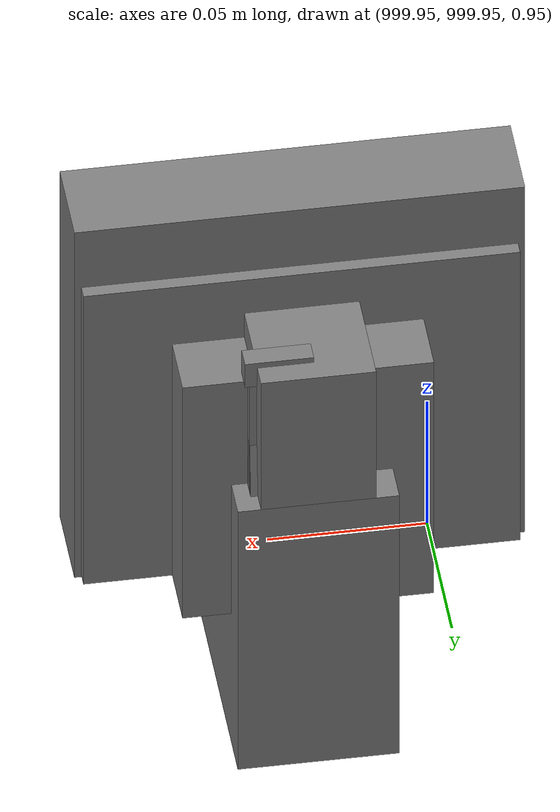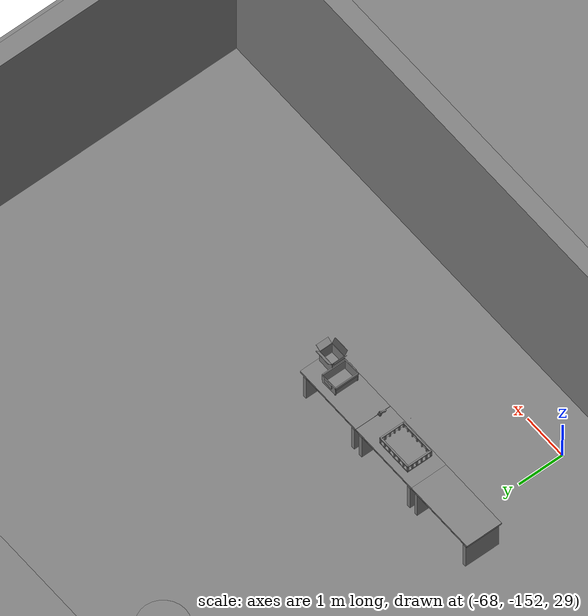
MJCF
<mujoco>
    <option gravity="0.000000000 0.000000000 -9.810000420" timestep="0.0049999999" integrator="implicitfast" density="1.225" viscosity="1.8000001e-05" noslip_iterations="10" iterations="100" sdf_iterations="50">
        <flag multiccd="disable"/>
    </option>
    <size memory="1000M"/>
    <compiler coordinate="local"/>
    <worldbody>
        <light cutoff="30" pos="0 1 1" dir="0 -1 -2"/>
        <light cutoff="30" pos="0 -1 1" dir="0 1 -2"/>
        <body pos="1000.000000000 1000.000000000 1.000000000" euler="0.000011953 0.000005123 -179.999984741" name="openloong_gripper_2f85_fix_base_usda_intel_box">
            <geom contype="1" conaffinity="1" density="1000" type="box" material="" rgba="0.500000000 0.500000000 0.500000000 1.000000000" solimp="0.899999976 0.949999988 0.001000000" friction="1.000000000 0.005000000 0.000100000" solref="0.020000000 1.000000000" margin="0" condim="3" group="0" pos="0.000000000 -0.000067139 0.000082284" quat="0.707106709 0.000000225 0.000000253 0.707106650" size="0.052800003 0.025300000 0.052800003" name="openloong_gripper_2f85_fix_base_usda_geom_4CF353C6_4DAA_4DB7_BDA5_880FF9AA9982"/>
            <freejoint name="openloong_gripper_2f85_fix_base_usda_intel_box_joint"/>
            <site size="0.005000000 0.005000000 0.005000000" rgba="0.500000000 0.500000000 0.500000000 1.000000000" pos="0.000000000 0.000000000 0.000000000" quat="0.999961913 0.008726500 0.000000000 0.000000000" group="0" type="sphere" name="openloong_gripper_2f85_fix_base_usda_intel_boxsite"/>
        </body>
        <body pos="-66.221458435 -148.931716919 31.164848328" euler="-73.387466431 -38.563747406 30.324836731" mocap="true" name="spotlight5_SpotLight"/>
        <body pos="1000.000000000 999.999938965 1.000000000" euler="0.000000000 0.000000000 180.000000000" name="openloong_gripper_2f85_fix_base_usda_intelcore_i5">
            <geom contype="1" conaffinity="1" density="1000" type="box" material="" rgba="0.500000000 0.500000000 0.500000000 1.000000000" solimp="0.899999976 0.949999988 0.001000000" friction="1.000000000 0.005000000 0.000100000" solref="0.020000000 1.000000000" margin="0" condim="3" group="0" pos="0.000000000 0.000000000 0.051722717" quat="0.707106709 0.000000000 0.000000000 -0.707106769" size="0.052800000 0.018080002 0.052800000" name="openloong_gripper_2f85_fix_base_usda_geom_54444D90_F1B6_45C8_B79D_580E50F92478"/>
            <freejoint name="openloong_gripper_2f85_fix_base_usda_intelcore_i5_joint"/>
            <site size="0.005000000 0.005000000 0.005000000" rgba="0.500000000 0.500000000 0.500000000 1.000000000" pos="0.000000000 0.000000000 0.000000000" quat="0.999961913 0.008726534 0.000000000 0.000000000" group="0" type="sphere" name="openloong_gripper_2f85_fix_base_usda_intelcore_i5site"/>
        </body>
        <body pos="-65.816711426 -149.036346436 31.163904190" euler="-80.475883484 21.044588089 -79.596343994" mocap="true" name="spotlight6_SpotLight"/>
        <body pos="1000.000000000 1000.000000000 1.000000000" euler="0.000000000 0.000000000 180.000000000" name="openloong_gripper_2f85_fix_base_usda_wifi_box">
            <geom contype="1" conaffinity="1" density="1000" type="box" material="" rgba="0.500000000 0.500000000 0.500000000 1.000000000" solimp="0.899999976 0.949999988 0.001000000" friction="1.000000000 0.005000000 0.000100000" solref="0.020000000 1.000000000" margin="0" condim="3" group="0" pos="0.000000000 0.000000000 0.058978677" quat="0.000000000 0.000000047 0.000000000 1.000000000" size="0.068499997 0.018999999 0.059000000" name="openloong_gripper_2f85_fix_base_usda_geom_F8BFE74D_4F6A_43D6_8DDB_8E383DAC0EB1"/>
            <freejoint name="openloong_gripper_2f85_fix_base_usda_wifi_box_joint"/>
            <site size="0.005000000 0.005000000 0.005000000" rgba="0.500000000 0.500000000 0.500000000 1.000000000" pos="0.000000000 0.000000000 0.000000000" quat="0.999961913 0.008726500 0.000000000 0.000000000" group="0" type="sphere" name="openloong_gripper_2f85_fix_base_usda_wifi_boxsite"/>
        </body>
        <body pos="1000.000000000 1000.000000000 1.000000000" euler="0.000000000 0.000000000 180.000000000" name="openloong_gripper_2f85_fix_base_usda_cpu_fan">
            <geom contype="1" conaffinity="1" density="1000" type="box" material="" rgba="0.500000000 0.500000000 0.500000000 1.000000000" solimp="0.899999976 0.949999988 0.001000000" friction="1.000000000 0.005000000 0.000100000" solref="0.020000000 1.000000000" margin="0" condim="3" group="0" pos="0.000000000 0.000000000 0.070034981" quat="0.000000000 0.000000000 0.000000000 1.000000000" size="0.070700005 0.014699999 0.070700005" name="openloong_gripper_2f85_fix_base_usda_geom_4330043B_5E8F_4623_841F_E15615E5DB19"/>
            <freejoint name="openloong_gripper_2f85_fix_base_usda_cpu_fan_joint"/>
            <site size="0.005000000 0.005000000 0.005000000" rgba="0.500000000 0.500000000 0.500000000 1.000000000" pos="0.000000000 0.000000000 0.000000000" quat="0.999961913 0.008726535 0.000000000 0.000000000" group="0" type="sphere" name="openloong_gripper_2f85_fix_base_usda_cpu_fancsite"/>
        </body>
        <body pos="-66.343162537 -149.329620361 31.170789719" euler="-119.588768005 48.532054901 -118.999168396" mocap="true" name="spotlight3_SpotLight"/>
        <body pos="1000.000000000 1000.000000000 1.000000000" euler="0.000000000 0.000000000 180.000000000" name="openloong_gripper_2f85_fix_base_usda_battery_01">
            <geom contype="1" conaffinity="1" density="1000" type="box" material="" rgba="0.500000000 0.500000000 0.500000000 1.000000000" solimp="0.899999976 0.949999988 0.001000000" friction="1.000000000 0.005000000 0.000100000" solref="0.020000000 1.000000000" margin="0" condim="3" group="0" pos="-0.011123657 -0.041940309 0.101691343" quat="1.000000000 0.000000000 0.000000000 0.000000000" size="0.010800000 0.003375000 0.004725000" name="openloong_gripper_2f85_fix_base_usda_geom_54066C0E_2C8F_4D37_B4C1_4802B8FEDBE6"/>
            <geom contype="1" conaffinity="1" density="1000" type="box" material="" rgba="0.500000000 0.500000000 0.500000000 1.000000000" solimp="0.899999976 0.949999988 0.001000000" friction="1.000000000 0.005000000 0.000100000" solref="0.020000000 1.000000000" margin="0" condim="3" group="0" pos="-0.010876465 -0.044247437 0.047066893" quat="0.998702705 -0.050920475 0.000000000 0.000000000" size="0.009450001 0.002700000 0.024975000" name="openloong_gripper_2f85_fix_base_usda_geom_4722477F_3508_4EA6_BDB9_674FFF5C838A"/>
            <geom contype="1" conaffinity="1" density="1000" type="box" material="" rgba="0.500000000 0.500000000 0.500000000 1.000000000" solimp="0.899999976 0.949999988 0.001000000" friction="1.000000000 0.005000000 0.000100000" solref="0.020000000 1.000000000" margin="0" condim="3" group="0" pos="-0.001235962 -0.000659180 0.047381196" quat="1.000000000 0.000000000 0.000000000 0.000000000" size="0.039420001 0.039150000 0.047250003" name="openloong_gripper_2f85_fix_base_usda_geom_831CBE91_56A5_43F4_94DF_9E2692AE72C4"/>
            <geom contype="1" conaffinity="1" density="1000" type="box" material="" rgba="0.500000000 0.500000000 0.500000000 1.000000000" solimp="0.899999976 0.949999988 0.001000000" friction="1.000000000 0.005000000 0.000100000" solref="0.020000000 1.000000000" margin="0" condim="3" group="0" pos="-0.010876465 -0.039138794 0.009851727" quat="1.000000000 0.000000000 0.000000000 0.000000000" size="0.009450001 0.010800000 0.013500000" name="openloong_gripper_2f85_fix_base_usda_geom_7A544085_5A45_4A1B_B1A3_DBFA908CA60A"/>
            <geom contype="1" conaffinity="1" density="1000" type="box" material="" rgba="0.500000000 0.500000000 0.500000000 1.000000000" solimp="0.899999976 0.949999988 0.001000000" friction="1.000000000 0.005000000 0.000100000" solref="0.020000000 1.000000000" margin="0" condim="3" group="0" pos="-0.010876465 -0.041528322 0.071508206" quat="1.000000000 0.000000000 0.000000000 0.000000000" size="0.009450001 0.002700000 0.027000001" name="openloong_gripper_2f85_fix_base_usda_geom_085AD4C0_7721_4174_8296_81D6991AA9D4"/>
            <freejoint name="openloong_gripper_2f85_fix_base_usda_battery_01_joint"/>
            <site size="0.005000000 0.005000000 0.005000000" rgba="0.500000000 0.500000000 0.500000000 1.000000000" pos="0.000000000 0.000000000 0.000000000" quat="0.999961913 0.008726500 0.000000000 0.000000000" group="0" type="sphere" name="openloong_gripper_2f85_fix_base_usda_battery_01site"/>
        </body>
        <body pos="-64.866622925 -149.383972168 30.183746338" euler="89.999984741 89.999946594 0.000000000" name="openloong_gripper_2f85_fix_base_usda_bluebox_01">
            <geom contype="1" conaffinity="1" density="1000" type="box" material="" rgba="0.500000000 0.500000000 0.500000000 1.000000000" solimp="0.899999976 0.949999988 0.001000000" friction="1.000000000 0.005000000 0.000100000" solref="0.020000000 1.000000000" margin="0" condim="3" group="0" pos="0.276580811 0.187225342 0.000068665" quat="0.707106948 0.000077471 0.707106352 0.000077486" size="0.100000001 0.057999998 0.010000000" name="openloong_gripper_2f85_fix_base_usda_geom_3B506333_E5EB_49A3_B820_2446F7D8993B"/>
            <geom contype="1" conaffinity="1" density="1000" type="box" material="" rgba="0.500000000 0.500000000 0.500000000 1.000000000" solimp="0.899999976 0.949999988 0.001000000" friction="1.000000000 0.005000000 0.000100000" solref="0.020000000 1.000000000" margin="0" condim="3" group="0" pos="0.000000000 0.002883911 0.000000000" quat="0.999999881 0.000000000 0.000000000 0.000000000" size="0.254000008 0.003000000 0.172000006" name="openloong_gripper_2f85_fix_base_usda_geom_E643540F_1F49_4701_9F79_CBE647AF7BD4"/>
            <geom contype="1" conaffinity="1" density="1000" type="box" material="" rgba="0.500000000 0.500000000 0.500000000 1.000000000" solimp="0.899999976 0.949999988 0.001000000" friction="1.000000000 0.005000000 0.000100000" solref="0.020000000 1.000000000" margin="0" condim="3" group="0" pos="0.000000000 0.124874115 0.173484802" quat="0.999796331 0.020176515 -0.000000015 0.000000030" size="0.259999990 0.119999997 0.007000000" name="openloong_gripper_2f85_fix_base_usda_geom_1F642737_9533_48B2_BB84_6106B7B38885"/>
            <geom contype="1" conaffinity="1" density="1000" type="box" material="" rgba="0.500000000 0.500000000 0.500000000 1.000000000" solimp="0.899999976 0.949999988 0.001000000" friction="1.000000000 0.005000000 0.000100000" solref="0.020000000 1.000000000" margin="0" condim="3" group="0" pos="0.000000000 0.124874115 -0.173469543" quat="0.999796331 -0.020176545 -0.000000015 0.000000000" size="0.259999990 0.119999997 0.007000000" name="openloong_gripper_2f85_fix_base_usda_geom_AB41686C_C43E_490F_8FA2_DEDBF742D963"/>
            <geom contype="1" conaffinity="1" density="1000" type="box" material="" rgba="0.500000000 0.500000000 0.500000000 1.000000000" solimp="0.899999976 0.949999988 0.001000000" friction="1.000000000 0.005000000 0.000100000" solref="0.020000000 1.000000000" margin="0" condim="3" group="0" pos="0.000000000 0.214008331 0.188980103" quat="0.999912977 0.013176724 0.000000015 0.000000000" size="0.259999990 0.029999999 0.012500000" name="openloong_gripper_2f85_fix_base_usda_geom_C3702C77_DE0B_4963_9BF7_560841029F77"/>
            <geom contype="1" conaffinity="1" density="1000" type="box" material="" rgba="0.500000000 0.500000000 0.500000000 1.000000000" solimp="0.899999976 0.949999988 0.001000000" friction="1.000000000 0.005000000 0.000100000" solref="0.020000000 1.000000000" margin="0" condim="3" group="0" pos="-0.258361816 0.125289917 0.001876831" quat="0.702796936 -0.020792112 0.710783124 0.020769298" size="0.189999998 0.119999997 0.009000000" name="openloong_gripper_2f85_fix_base_usda_geom_3C50D46C_358B_43C2_BA93_D4D8F2FD9AF4"/>
            <geom contype="1" conaffinity="1" density="1000" type="box" material="" rgba="0.500000000 0.500000000 0.500000000 1.000000000" solimp="0.899999976 0.949999988 0.001000000" friction="1.000000000 0.005000000 0.000100000" solref="0.020000000 1.000000000" margin="0" condim="3" group="0" pos="0.000000000 0.214008331 -0.188980103" quat="0.999912977 -0.013176769 0.000000030 0.000000015" size="0.259999990 0.029999999 0.012500000" name="openloong_gripper_2f85_fix_base_usda_geom_AC1E2316_CEC6_40C4_A81F_F6487242CD15"/>
            <geom contype="1" conaffinity="1" density="1000" type="box" material="" rgba="0.500000000 0.500000000 0.500000000 1.000000000" solimp="0.899999976 0.949999988 0.001000000" friction="1.000000000 0.005000000 0.000100000" solref="0.020000000 1.000000000" margin="0" condim="3" group="0" pos="-0.276611328 0.187225342 0.000068665" quat="0.707106650 0.000077441 0.707106709 0.000077456" size="0.100000001 0.057999998 0.010000000" name="openloong_gripper_2f85_fix_base_usda_geom_6BCC0C73_A4F3_4B39_BDBF_5EFF9C106DCC"/>
            <geom contype="1" conaffinity="1" density="1000" type="box" material="" rgba="0.500000000 0.500000000 0.500000000 1.000000000" solimp="0.899999976 0.949999988 0.001000000" friction="1.000000000 0.005000000 0.000100000" solref="0.020000000 1.000000000" margin="0" condim="3" group="0" pos="0.258331299 0.125289917 0.001876831" quat="0.702851415 0.018856421 0.710823774 -0.019329369" size="0.189999998 0.119999997 0.009000000" name="openloong_gripper_2f85_fix_base_usda_geom_02C27BCB_2440_4D0E_BA9D_681139923E9F"/>
            <freejoint name="openloong_gripper_2f85_fix_base_usda_bluebox_01_joint"/>
            <site size="0.005000000 0.005000000 0.005000000" rgba="0.500000000 0.500000000 0.500000000 1.000000000" pos="0.000000000 0.000000000 0.000000000" quat="0.999961913 0.008726534 0.000000000 0.000000000" group="0" type="sphere" name="openloong_gripper_2f85_fix_base_usda_bluebox_01site"/>
        </body>
        <body pos="-64.496299744 -149.491867065 30.235729218" euler="0.000000000 0.000000000 89.999946594" name="openloong_gripper_2f85_fix_base_usda_cardboardbox_01">
            <geom contype="1" conaffinity="1" density="1000" type="box" material="" rgba="0.500000000 0.500000000 0.500000000 1.000000000" solimp="0.899999976 0.949999988 0.001000000" friction="1.000000000 0.005000000 0.000100000" solref="0.020000000 1.000000000" margin="0" condim="3" group="0" pos="-0.003166199 -0.004086494 0.005052090" quat="1.000000000 0.000000000 0.000000000 0.000000000" size="0.142499998 0.177500010 0.005000000" name="openloong_gripper_2f85_fix_base_usda_geom_6005C631_6A09_4F6C_988C_05B49FC40432"/>
            <geom contype="1" conaffinity="1" density="1000" type="box" material="" rgba="0.500000000 0.500000000 0.500000000 1.000000000" solimp="0.899999976 0.949999988 0.001000000" friction="1.000000000 0.005000000 0.000100000" solref="0.020000000 1.000000000" margin="0" condim="3" group="0" pos="-0.003166199 0.170316696 0.150570869" quat="1.000000000 0.000000000 0.000000000 0.000000000" size="0.142499998 0.005000000 0.149999991" name="openloong_gripper_2f85_fix_base_usda_geom_13BB9FFB_19A7_4E9C_A4CF_A6C0F4F1DFE9"/>
            <geom contype="1" conaffinity="1" density="1000" type="box" material="" rgba="0.500000000 0.500000000 0.500000000 1.000000000" solimp="0.899999976 0.949999988 0.001000000" friction="1.000000000 0.005000000 0.000100000" solref="0.020000000 1.000000000" margin="0" condim="3" group="0" pos="-0.147399902 -0.005307198 0.150570869" quat="1.000000000 0.000000000 0.000000000 0.000000000" size="0.005000000 0.177500010 0.149999991" name="openloong_gripper_2f85_fix_base_usda_geom_529102DC_082B_43F2_8AA1_EFCEA678C99E"/>
            <geom contype="1" conaffinity="1" density="1000" type="box" material="" rgba="0.500000000 0.500000000 0.500000000 1.000000000" solimp="0.899999976 0.949999988 0.001000000" friction="1.000000000 0.005000000 0.000100000" solref="0.020000000 1.000000000" margin="0" condim="3" group="0" pos="0.140275955 -0.005307198 0.150570869" quat="1.000000000 0.000000000 0.000000000 0.000000000" size="0.005000000 0.177500010 0.149999991" name="openloong_gripper_2f85_fix_base_usda_geom_3D27C0F0_1DF2_4C39_AE4F_F4606B679DDC"/>
            <geom contype="1" conaffinity="1" density="1000" type="box" material="" rgba="0.500000000 0.500000000 0.500000000 1.000000000" solimp="0.899999976 0.949999988 0.001000000" friction="1.000000000 0.005000000 0.000100000" solref="0.020000000 1.000000000" margin="0" condim="3" group="0" pos="-0.003166199 -0.181550980 0.150570869" quat="1.000000000 0.000000000 0.000000000 0.000000000" size="0.142499998 0.005000000 0.149999991" name="openloong_gripper_2f85_fix_base_usda_geom_D5082BBC_8B89_4997_93DD_27C08FB43321"/>
            <freejoint name="openloong_gripper_2f85_fix_base_usda_cardboardbox_01_joint"/>
            <site size="0.005000000 0.005000000 0.005000000" rgba="0.500000000 0.500000000 0.500000000 1.000000000" pos="0.000000000 0.000000000 0.000000000" quat="0.999961913 0.008726535 0.000000000 0.000000000" group="0" type="sphere" name="openloong_gripper_2f85_fix_base_usda_site_11F53B57_30D9_49BB_AAF5_7BCCD0EFE858"/>
            <body pos="0.139160156 -0.004048347 0.301930904" euler="-179.999954224 49.383502960 179.999954224" name="openloong_gripper_2f85_fix_base_usda_A1_006">
                <geom contype="1" conaffinity="1" density="1000" type="box" material="" rgba="0.500000000 0.500000000 0.500000000 1.000000000" solimp="0.899999976 0.949999988 0.001000000" friction="1.000000000 0.005000000 0.000100000" solref="0.020000000 1.000000000" margin="0" condim="3" group="0" pos="-0.071587563 0.000009537 0.001745224" quat="0.999999881 0.000000000 0.000000000 0.000000000" size="0.071249999 0.179999992 0.002500000" name="openloong_gripper_2f85_fix_base_usda_geom_17853071_3429_4353_8ECF_C7A211958058"/>
                <joint armature="0" stiffness="0.07" damping="0.0099999998" axis="0.000000 1.000000 0.000000" type="hinge" name="openloong_gripper_2f85_fix_base_usda_A1_006"/>
            </body>
            <body pos="-0.145902634 -0.004086494 0.301938057" euler="-180.000000000 -60.000011444 -180.000000000" name="openloong_gripper_2f85_fix_base_usda_A2_006">
                <geom contype="1" conaffinity="1" density="1000" type="box" material="" rgba="0.500000000 0.500000000 0.500000000 1.000000000" solimp="0.899999976 0.949999988 0.001000000" friction="1.000000000 0.005000000 0.000100000" solref="0.020000000 1.000000000" margin="0" condim="3" group="0" pos="0.071268082 0.000009537 0.002717972" quat="0.000002921 0.000000000 -0.000000030 0.999999881" size="0.071249999 0.179999992 0.002500000" name="openloong_gripper_2f85_fix_base_usda_geom_CB065A30_7C9E_46E2_A9DB_A9FD67F7A158"/>
                <joint armature="0" stiffness="0.07" damping="0.0099999998" axis="0.000000 1.000000 0.000000" type="hinge" name="openloong_gripper_2f85_fix_base_usda_A2_006"/>
            </body>
            <body pos="-0.003385544 0.175991058 0.301930904" euler="-125.858116150 -0.000004561 0.000002331" name="openloong_gripper_2f85_fix_base_usda_B2_006">
                <geom contype="1" conaffinity="1" density="1000" type="box" material="" rgba="0.500000000 0.500000000 0.500000000 1.000000000" solimp="0.899999976 0.949999988 0.001000000" friction="1.000000000 0.005000000 0.000100000" solref="0.020000000 1.000000000" margin="0" condim="3" group="0" pos="0.000009537 -0.070939064 -0.002470016" quat="0.999614120 0.027776197 -0.000000015 0.000000030" size="0.137500003 0.064999998 0.005000000" name="openloong_gripper_2f85_fix_base_usda_geom_27366642_2D5A_4DE7_921A_85CB3D6AFF27"/>
                <joint armature="0" stiffness="0.07" damping="0.0099999998" axis="1.000000 0.000000 0.000000" type="hinge" name="openloong_gripper_2f85_fix_base_usda_B2_006"/>
            </body>
            <body pos="-0.003385544 -0.184140205 0.301938057" euler="147.805557251 0.000000000 0.000000000" name="openloong_gripper_2f85_fix_base_usda_B1_006">
                <geom contype="1" conaffinity="1" density="1000" type="box" material="" rgba="0.500000000 0.500000000 0.500000000 1.000000000" solimp="0.899999976 0.949999988 0.001000000" friction="1.000000000 0.005000000 0.000100000" solref="0.020000000 1.000000000" margin="0" condim="3" group="0" pos="-0.000028610 0.070202351 -0.002703667" quat="0.999614179 -0.027776167 0.000000000 0.000000000" size="0.137500003 0.064999998 0.005000000" name="openloong_gripper_2f85_fix_base_usda_geom_A4F0EEF0_7451_450B_9083_7F52F03BB063"/>
                <joint armature="0" stiffness="0.07" damping="0.0099999998" axis="1.000000 0.000000 0.000000" type="hinge" name="openloong_gripper_2f85_fix_base_usda_B1_006"/>
            </body>
        </body>
        <body pos="-65.882858276 -149.481979370 30.229999542" euler="-64.487716675 0.000000000 0.000000000" name="openloong_gripper_2f85_fix_base_usda_Barcode">
            <geom contype="1" conaffinity="1" density="1000" type="box" material="" rgba="0.500000000 0.500000000 0.500000000 1.000000000" solimp="0.899999976 0.949999988 0.001000000" friction="1.000000000 0.005000000 0.000100000" solref="0.020000000 1.000000000" margin="0" condim="3" group="0" pos="0.000000000 0.013038635 0.001419067" quat="0.000000000 0.000000000 0.000000000 1.000000119" size="0.034000002 0.010000000 0.017999999" name="openloong_gripper_2f85_fix_base_usda_geom_B32A31AE_60EA_4516_BF42_B681E229BD0E"/>
            <geom contype="1" conaffinity="1" density="1000" type="box" material="" rgba="0.500000000 0.500000000 0.500000000 1.000000000" solimp="0.899999976 0.949999988 0.001000000" friction="1.000000000 0.005000000 0.000100000" solref="0.020000000 1.000000000" margin="0" condim="3" group="0" pos="0.000000000 -0.035301208 -0.007095337" quat="0.000000000 0.000000000 -0.043619365 0.999048233" size="0.028999999 0.010000000 0.020000000" name="openloong_gripper_2f85_fix_base_usda_geom_3B206F6C_E07E_405D_8EFA_51CBD622C366"/>
            <geom contype="1" conaffinity="1" density="1000" type="box" material="" rgba="0.500000000 0.500000000 0.500000000 1.000000000" solimp="0.899999976 0.949999988 0.001000000" friction="1.000000000 0.005000000 0.000100000" solref="0.020000000 1.000000000" margin="0" condim="3" group="0" pos="0.000000000 -0.043411255 -0.011749268" quat="0.922262907 0.386563420 0.000000000 0.000000000" size="0.026000001 0.010000000 0.020000000" name="openloong_gripper_2f85_fix_base_usda_geom_9E32E971_0D6D_492A_88FD_19CB700EEB4B"/>
            <geom contype="1" conaffinity="1" density="1000" type="box" material="" rgba="0.500000000 0.500000000 0.500000000 1.000000000" solimp="0.899999976 0.949999988 0.001000000" friction="1.000000000 0.005000000 0.000100000" solref="0.020000000 1.000000000" margin="0" condim="3" group="0" pos="0.000000000 -0.016967773 -0.031860352" quat="0.000000000 0.000000000 0.000000000 1.000000119" size="0.008000000 0.010000000 0.013000000" name="openloong_gripper_2f85_fix_base_usda_geom_FEAC87A7_BC54_44D2_9D7E_57E345C02BB1"/>
            <geom contype="1" conaffinity="1" density="1000" type="box" material="" rgba="0.500000000 0.500000000 0.500000000 1.000000000" solimp="0.899999976 0.949999988 0.001000000" friction="1.000000000 0.005000000 0.000100000" solref="0.020000000 1.000000000" margin="0" condim="3" group="0" pos="0.000000000 -0.001869202 0.000312805" quat="0.953716993 0.300705761 0.000000000 0.000000000" size="0.032000002 0.010000000 0.018999999" name="openloong_gripper_2f85_fix_base_usda_geom_0121F094_2A45_49F1_975E_01A352DCAE2B"/>
            <geom contype="1" conaffinity="1" density="1000" type="box" material="" rgba="0.500000000 0.500000000 0.500000000 1.000000000" solimp="0.899999976 0.949999988 0.001000000" friction="1.000000000 0.005000000 0.000100000" solref="0.020000000 1.000000000" margin="0" condim="3" group="0" pos="0.000000000 -0.019531250 -0.003173828" quat="0.953716993 0.300705761 0.000000000 0.000000000" size="0.030999999 0.010000000 0.020000000" name="openloong_gripper_2f85_fix_base_usda_geom_4B5309FC_A7E0_4CCE_A258_D89E1CB4CEFD"/>
            <geom contype="1" conaffinity="1" density="1000" type="box" material="" rgba="0.500000000 0.500000000 0.500000000 1.000000000" solimp="0.899999976 0.949999988 0.001000000" friction="1.000000000 0.005000000 0.000100000" solref="0.020000000 1.000000000" margin="0" condim="3" group="0" pos="0.000000000 -0.035301208 -0.007095337" quat="0.953716993 0.300705761 0.000000000 0.000000000" size="0.028999999 0.010000000 0.020000000" name="openloong_gripper_2f85_fix_base_usda_geom_7FF2B2A9_E465_4D30_851C_C5C5F26B5BBC"/>
            <geom contype="1" conaffinity="1" density="1000" type="box" material="" rgba="0.500000000 0.500000000 0.500000000 1.000000000" solimp="0.899999976 0.949999988 0.001000000" friction="1.000000000 0.005000000 0.000100000" solref="0.020000000 1.000000000" margin="0" condim="3" group="0" pos="0.000000000 -0.042617798 -0.071121216" quat="0.000000000 0.000000000 0.000000000 1.000000119" size="0.013000000 0.021000000 0.059999999" name="openloong_gripper_2f85_fix_base_usda_geom_5B67C2E9_2CCC_47B4_8201_5048362EA365"/>
            <freejoint name="openloong_gripper_2f85_fix_base_usda_Barcode_joint"/>
            <site size="0.005000000 0.005000000 0.005000000" rgba="0.500000000 0.500000000 0.500000000 1.000000000" pos="0.000000000 0.000000000 0.000000000" quat="1.000000000 0.000000000 0.000000000 0.000000000" group="0" type="sphere" name="openloong_gripper_2f85_fix_base_usda_Barcode_site"/>
        </body>
        <body pos="-66.745018005 -149.392349243 30.184000015" euler="0.000000000 0.000000000 89.999946594" name="[22330734727291]_Basket_01">
            <geom contype="1" conaffinity="1" density="1000" type="box" material="" rgba="0.500000000 0.500000000 0.500000000 1.000000000" solimp="0.899999976 0.949999988 0.001000000" friction="1.000000000 0.005000000 0.000100000" solref="0.020000000 1.000000000" margin="0" condim="3" group="0" pos="-0.052425385 0.389207840 0.089787483" quat="0.707107008 0.000000000 0.000000000 0.707106411" size="0.014249999 0.014249999 0.059999999" name="[22330734727291]_geom_5F0F7F80_84CD_4810_ACEC_D4CD0FF1A15B"/>
            <geom contype="1" conaffinity="1" density="1000" type="box" material="" rgba="0.500000000 0.500000000 0.500000000 1.000000000" solimp="0.899999976 0.949999988 0.001000000" friction="1.000000000 0.005000000 0.000100000" solref="0.020000000 1.000000000" margin="0" condim="3" group="0" pos="0.264015198 -0.133043289 0.089787483" quat="0.707107008 0.000000000 0.000000000 0.707106411" size="0.014249999 0.014249999 0.059999999" name="[22330734727291]_geom_ACCD69FC_A3E1_4D52_9551_41A15F0B840D"/>
            <geom contype="1" conaffinity="1" density="1000" type="box" material="" rgba="0.500000000 0.500000000 0.500000000 1.000000000" solimp="0.899999976 0.949999988 0.001000000" friction="1.000000000 0.005000000 0.000100000" solref="0.020000000 1.000000000" margin="0" condim="3" group="0" pos="-0.264015198 -0.265548706 0.089793205" quat="0.707107008 0.000000000 0.000000000 0.707106411" size="0.014249999 0.014249999 0.059999999" name="[22330734727291]_geom_3C89E2C0_ADF1_4418_B35C_52AD1A4A9BF5"/>
            <geom contype="1" conaffinity="1" density="1000" type="box" material="" rgba="0.500000000 0.500000000 0.500000000 1.000000000" solimp="0.899999976 0.949999988 0.001000000" friction="1.000000000 0.005000000 0.000100000" solref="0.020000000 1.000000000" margin="0" condim="3" group="0" pos="-0.160263062 -0.389322281 0.089793205" quat="0.707107008 0.000000000 0.000000000 0.707106411" size="0.014249999 0.014249999 0.059999999" name="[22330734727291]_geom_96CF8806_D127_4706_9A7C_5A2B359AC8A4"/>
            <geom contype="1" conaffinity="1" density="1000" type="box" material="" rgba="0.500000000 0.500000000 0.500000000 1.000000000" solimp="0.899999976 0.949999988 0.001000000" friction="1.000000000 0.005000000 0.000100000" solref="0.020000000 1.000000000" margin="0" condim="3" group="0" pos="0.162265778 -0.389322281 0.089787483" quat="0.707107008 0.000000000 0.000000000 0.707106411" size="0.014249999 0.014249999 0.059999999" name="[22330734727291]_geom_C5ACBA76_D127_4CEB_B58B_C9046B14BE03"/>
            <geom contype="1" conaffinity="1" density="1000" type="box" material="" rgba="0.500000000 0.500000000 0.500000000 1.000000000" solimp="0.899999976 0.949999988 0.001000000" friction="1.000000000 0.005000000 0.000100000" solref="0.020000000 1.000000000" margin="0" condim="3" group="0" pos="0.264015198 0.389207840 0.089787483" quat="0.707107008 0.000000000 0.000000000 0.707106411" size="0.014249999 0.014249999 0.059999999" name="[22330734727291]_geom_9F85E210_F8EA_4EA0_8ADD_D7097189752A"/>
            <geom contype="1" conaffinity="1" density="1000" type="box" material="" rgba="0.500000000 0.500000000 0.500000000 1.000000000" solimp="0.899999976 0.949999988 0.001000000" friction="1.000000000 0.005000000 0.000100000" solref="0.020000000 1.000000000" margin="0" condim="3" group="0" pos="-0.264015198 -0.133043289 0.089793205" quat="0.707107008 0.000000000 0.000000000 0.707106411" size="0.014249999 0.014249999 0.059999999" name="[22330734727291]_geom_E2258916_3E6D_4529_8CB4_FDC60EAD481B"/>
            <geom contype="1" conaffinity="1" density="1000" type="box" material="" rgba="0.500000000 0.500000000 0.500000000 1.000000000" solimp="0.899999976 0.949999988 0.001000000" friction="1.000000000 0.005000000 0.000100000" solref="0.020000000 1.000000000" margin="0" condim="3" group="0" pos="-0.264026642 0.269256592 0.089793205" quat="0.707107008 0.000000000 0.000000000 0.707106411" size="0.014249999 0.014249999 0.059999999" name="[22330734727291]_geom_DD488FCB_E188_42A0_9953_9DD579B7725A"/>
            <geom contype="1" conaffinity="1" density="1000" type="box" material="" rgba="0.500000000 0.500000000 0.500000000 1.000000000" solimp="0.899999976 0.949999988 0.001000000" friction="1.000000000 0.005000000 0.000100000" solref="0.020000000 1.000000000" margin="0" condim="3" group="0" pos="0.054462433 0.389207840 0.089787483" quat="0.707107008 0.000000000 0.000000000 0.707106411" size="0.014249999 0.014249999 0.059999999" name="[22330734727291]_geom_5CA4A1B4_BA6A_4BA7_9B7A_5DDEFAC914E5"/>
            <geom contype="1" conaffinity="1" density="1000" type="box" material="" rgba="0.500000000 0.500000000 0.500000000 1.000000000" solimp="0.899999976 0.949999988 0.001000000" friction="1.000000000 0.005000000 0.000100000" solref="0.020000000 1.000000000" margin="0" condim="3" group="0" pos="0.054462433 -0.389322281 0.089787483" quat="0.707107008 0.000000000 0.000000000 0.707106411" size="0.014249999 0.014249999 0.059999999" name="[22330734727291]_geom_E4A9C981_AA15_4F3C_9E83_576C98456ABA"/>
            <geom contype="1" conaffinity="1" density="1000" type="box" material="" rgba="0.500000000 0.500000000 0.500000000 1.000000000" solimp="0.899999976 0.949999988 0.001000000" friction="1.000000000 0.005000000 0.000100000" solref="0.020000000 1.000000000" margin="0" condim="3" group="0" pos="0.264015198 0.269256592 0.089793205" quat="0.707107008 0.000000000 0.000000000 0.707106411" size="0.014249999 0.014249999 0.059999999" name="[22330734727291]_geom_9255EDA0_2FC4_460D_ACB3_597D013C0D50"/>
            <geom contype="1" conaffinity="1" density="1000" type="box" material="" rgba="0.500000000 0.500000000 0.500000000 1.000000000" solimp="0.899999976 0.949999988 0.001000000" friction="1.000000000 0.005000000 0.000100000" solref="0.020000000 1.000000000" margin="0" condim="3" group="0" pos="0.264015198 -0.389322281 0.089787483" quat="0.707107008 0.000000000 0.000000000 0.707106411" size="0.014249999 0.014249999 0.059999999" name="[22330734727291]_geom_1466A7CF_5629_48BE_983C_7231211C2809"/>
            <geom contype="1" conaffinity="1" density="1000" type="box" material="" rgba="0.500000000 0.500000000 0.500000000 1.000000000" solimp="0.899999976 0.949999988 0.001000000" friction="1.000000000 0.005000000 0.000100000" solref="0.020000000 1.000000000" margin="0" condim="3" group="0" pos="0.000000000 0.000000000 0.015998840" quat="0.707107008 0.000000000 0.000000000 0.707106411" size="0.403499991 0.279000014 0.015750000" name="[22330734727291]_geom_BBB7E4B9_2F4A_4263_8961_3AD84CBB88BE"/>
            <geom contype="1" conaffinity="1" density="1000" type="box" material="" rgba="0.500000000 0.500000000 0.500000000 1.000000000" solimp="0.899999976 0.949999988 0.001000000" friction="1.000000000 0.005000000 0.000100000" solref="0.020000000 1.000000000" margin="0" condim="3" group="0" pos="0.000000000 -0.389476776 0.163619041" quat="0.707107008 0.000000000 0.000000000 0.707106411" size="0.015000000 0.277500004 0.015750000" name="[22330734727291]_geom_090C5C43_C5BC_40AA_80E1_73EE5F164245"/>
            <geom contype="1" conaffinity="1" density="1000" type="box" material="" rgba="0.500000000 0.500000000 0.500000000 1.000000000" solimp="0.899999976 0.949999988 0.001000000" friction="1.000000000 0.005000000 0.000100000" solref="0.020000000 1.000000000" margin="0" condim="3" group="0" pos="0.162265778 0.389207840 0.089787483" quat="0.707107008 0.000000000 0.000000000 0.707106411" size="0.014249999 0.014249999 0.059999999" name="[22330734727291]_geom_DD4532C1_2993_4DD6_ABD2_4EDAAF866A46"/>
            <geom contype="1" conaffinity="1" density="1000" type="box" material="" rgba="0.500000000 0.500000000 0.500000000 1.000000000" solimp="0.899999976 0.949999988 0.001000000" friction="1.000000000 0.005000000 0.000100000" solref="0.020000000 1.000000000" margin="0" condim="3" group="0" pos="0.000000000 0.389471054 0.163619041" quat="0.707107008 0.000000000 0.000000000 0.707106411" size="0.015000000 0.277500004 0.015750000" name="[22330734727291]_geom_27FA5D0E_F874_43F0_901A_7DEC8CF46AAA"/>
            <geom contype="1" conaffinity="1" density="1000" type="box" material="" rgba="0.500000000 0.500000000 0.500000000 1.000000000" solimp="0.899999976 0.949999988 0.001000000" friction="1.000000000 0.005000000 0.000100000" solref="0.020000000 1.000000000" margin="0" condim="3" group="0" pos="-0.263511658 0.000000000 0.163619041" quat="0.707107008 0.000000000 0.000000000 0.707106411" size="0.403499991 0.015000000 0.015750000" name="[22330734727291]_geom_0D0FB356_BC21_40AA_BF93_82AA28AA29A1"/>
            <geom contype="1" conaffinity="1" density="1000" type="box" material="" rgba="0.500000000 0.500000000 0.500000000 1.000000000" solimp="0.899999976 0.949999988 0.001000000" friction="1.000000000 0.005000000 0.000100000" solref="0.020000000 1.000000000" margin="0" condim="3" group="0" pos="-0.264015198 0.141334534 0.089793205" quat="0.707107008 0.000000000 0.000000000 0.707106411" size="0.014249999 0.014249999 0.059999999" name="[22330734727291]_geom_B5677FB9_A569_4872_9867_6D55A0DC9B84"/>
            <geom contype="1" conaffinity="1" density="1000" type="box" material="" rgba="0.500000000 0.500000000 0.500000000 1.000000000" solimp="0.899999976 0.949999988 0.001000000" friction="1.000000000 0.005000000 0.000100000" solref="0.020000000 1.000000000" margin="0" condim="3" group="0" pos="0.264015198 -0.265548706 0.089787483" quat="0.707107008 0.000000000 0.000000000 0.707106411" size="0.014249999 0.014249999 0.059999999" name="[22330734727291]_geom_4CEF2BA2_8C1D_4A73_BA12_E1FEAAAF7262"/>
            <geom contype="1" conaffinity="1" density="1000" type="box" material="" rgba="0.500000000 0.500000000 0.500000000 1.000000000" solimp="0.899999976 0.949999988 0.001000000" friction="1.000000000 0.005000000 0.000100000" solref="0.020000000 1.000000000" margin="0" condim="3" group="0" pos="-0.160263062 0.389207840 0.089787483" quat="0.707107008 0.000000000 0.000000000 0.707106411" size="0.014249999 0.014249999 0.059999999" name="[22330734727291]_geom_761CCD03_D763_4797_BCC3_8F0C34404E4B"/>
            <geom contype="1" conaffinity="1" density="1000" type="box" material="" rgba="0.500000000 0.500000000 0.500000000 1.000000000" solimp="0.899999976 0.949999988 0.001000000" friction="1.000000000 0.005000000 0.000100000" solref="0.020000000 1.000000000" margin="0" condim="3" group="0" pos="-0.052425385 -0.389322281 0.089787483" quat="0.707107008 0.000000000 0.000000000 0.707106411" size="0.014249999 0.014249999 0.059999999" name="[22330734727291]_geom_8822E3A7_F749_468C_8437_609580FFC196"/>
            <geom contype="1" conaffinity="1" density="1000" type="box" material="" rgba="0.500000000 0.500000000 0.500000000 1.000000000" solimp="0.899999976 0.949999988 0.001000000" friction="1.000000000 0.005000000 0.000100000" solref="0.020000000 1.000000000" margin="0" condim="3" group="0" pos="-0.264026642 -0.389322281 0.089793205" quat="0.707107008 0.000000000 0.000000000 0.707106411" size="0.014249999 0.014249999 0.059999999" name="[22330734727291]_geom_9A6F4656_7ACD_48E6_973F_659CF833996C"/>
            <geom contype="1" conaffinity="1" density="1000" type="box" material="" rgba="0.500000000 0.500000000 0.500000000 1.000000000" solimp="0.899999976 0.949999988 0.001000000" friction="1.000000000 0.005000000 0.000100000" solref="0.020000000 1.000000000" margin="0" condim="3" group="0" pos="0.264015198 0.141334534 0.089787483" quat="0.707107008 0.000000000 0.000000000 0.707106411" size="0.014249999 0.014249999 0.059999999" name="[22330734727291]_geom_BB74A9DD_A1B5_433E_BF1D_C61C99CC2875"/>
            <geom contype="1" conaffinity="1" density="1000" type="box" material="" rgba="0.500000000 0.500000000 0.500000000 1.000000000" solimp="0.899999976 0.949999988 0.001000000" friction="1.000000000 0.005000000 0.000100000" solref="0.020000000 1.000000000" margin="0" condim="3" group="0" pos="-0.264015198 0.389207840 0.089793205" quat="0.707107008 0.000000000 0.000000000 0.707106411" size="0.014249999 0.014249999 0.059999999" name="[22330734727291]_geom_E63140E7_AA0F_4D22_9A24_3F2541DA5E56"/>
            <geom contype="1" conaffinity="1" density="1000" type="box" material="" rgba="0.500000000 0.500000000 0.500000000 1.000000000" solimp="0.899999976 0.949999988 0.001000000" friction="1.000000000 0.005000000 0.000100000" solref="0.020000000 1.000000000" margin="0" condim="3" group="0" pos="0.264015198 0.004480362 0.089787483" quat="0.707107008 0.000000000 0.000000000 0.707106411" size="0.014249999 0.014249999 0.059999999" name="[22330734727291]_geom_37DC6CF2_0DAA_4076_AB44_CFE1F5355350"/>
            <geom contype="1" conaffinity="1" density="1000" type="box" material="" rgba="0.500000000 0.500000000 0.500000000 1.000000000" solimp="0.899999976 0.949999988 0.001000000" friction="1.000000000 0.005000000 0.000100000" solref="0.020000000 1.000000000" margin="0" condim="3" group="0" pos="0.263694763 -0.000011444 0.163619041" quat="0.707107008 0.000000000 0.000000000 0.707106411" size="0.403499991 0.015000000 0.015750000" name="[22330734727291]_geom_6AAFC239_1A06_4174_923E_9D8DDFDD0B85"/>
            <geom contype="1" conaffinity="1" density="1000" type="box" material="" rgba="0.500000000 0.500000000 0.500000000 1.000000000" solimp="0.899999976 0.949999988 0.001000000" friction="1.000000000 0.005000000 0.000100000" solref="0.020000000 1.000000000" margin="0" condim="3" group="0" pos="-0.264015198 0.004480362 0.089793205" quat="0.707107008 0.000000000 0.000000000 0.707106411" size="0.014249999 0.014249999 0.059999999" name="[22330734727291]_geom_B7D276DD_4704_4051_ACAF_60F0EB9590E4"/>
            <freejoint name="[22330734727291]_joint_88ED231E_F095_4544_9800_25CE204B383F"/>
        </body>
        <body pos="0.000000000 0.000000000 0.000000000" euler="0.000000000 0.000000000 0.000000000" name="Static Objects_Static Objects">
            <geom contype="1" conaffinity="1" density="1000" type="box" material="" rgba="0.500000000 0.500000000 0.500000000 1.000000000" solimp="0.899999976 0.949999988 0.001000000" friction="1.000000000 0.005000000 0.000100000" solref="0.020000000 1.000000000" margin="0" condim="3" group="0" pos="-67.544113159 -149.365814209 29.727830887" quat="0.500000417 0.499999970 0.499999553 0.499999970" size="0.381000012 0.319999993 0.041000001" name="Static Objects_geom_758A16A2_081B_4A2D_BBEE_42BD85826D4B"/>
            <geom contype="1" conaffinity="1" density="1000" type="box" material="" rgba="0.500000000 0.500000000 0.500000000 1.000000000" solimp="0.899999976 0.949999988 0.001000000" friction="1.000000000 0.005000000 0.000100000" solref="0.020000000 1.000000000" margin="0" condim="3" group="0" pos="-68.239501953 -149.365814209 30.086868286" quat="0.500000417 0.499999970 0.499999553 0.499999970" size="0.370999992 0.039500002 0.745000005" name="Static Objects_geom_EADC2E6B_AC86_4C61_95A4_734AE568DED4"/>
            <geom contype="1" conaffinity="1" density="1000" type="box" material="" rgba="0.500000000 0.500000000 0.500000000 1.000000000" solimp="0.899999976 0.949999988 0.001000000" friction="1.000000000 0.005000000 0.000100000" solref="0.020000000 1.000000000" margin="0" condim="3" group="0" pos="-68.239501953 -149.365814209 30.147235870" quat="0.500000417 0.499999970 0.499999553 0.499999970" size="0.400000006 0.022000000 0.800000012" name="Static Objects_geom_11772927_4F7B_457F_91A1_1E2D10DAECBE"/>
            <geom contype="1" conaffinity="1" density="1000" type="box" material="" rgba="0.500000000 0.500000000 0.500000000 1.000000000" solimp="0.899999976 0.949999988 0.001000000" friction="1.000000000 0.005000000 0.000100000" solref="0.020000000 1.000000000" margin="0" condim="3" group="0" pos="-68.934890747 -149.365814209 29.727830887" quat="0.500000417 0.499999970 0.499999553 0.499999970" size="0.381000012 0.319999993 0.041000001" name="Static Objects_geom_BFB11F91_9EE2_4CB2_B425_5D60D8F6F1C2"/>
            <geom contype="1" conaffinity="1" density="1000" type="box" material="" rgba="0.500000000 0.500000000 0.500000000 1.000000000" solimp="0.899999976 0.949999988 0.001000000" friction="1.000000000 0.005000000 0.000100000" solref="0.020000000 1.000000000" margin="0" condim="3" group="0" pos="-68.239501953 -149.365814209 29.561563492" quat="0.500000417 0.499999970 0.499999553 0.499999970" size="0.020000000 0.022000000 0.660000026" name="Static Objects_geom_24529A66_D911_4360_81D4_5737FD5A1277"/>
            <geom contype="1" conaffinity="1" density="1000" type="box" material="" rgba="0.500000000 0.500000000 0.500000000 1.000000000" solimp="0.899999976 0.949999988 0.001000000" friction="1.000000000 0.005000000 0.000100000" solref="0.020000000 1.000000000" margin="0" condim="3" group="0" pos="-65.945671082 -149.365814209 29.727830887" quat="0.500000417 0.499999970 0.499999553 0.499999970" size="0.381000012 0.319999993 0.041000001" name="Static Objects_geom_BCA9300D_A536_4F45_88CF_7BD568763236"/>
            <geom contype="1" conaffinity="1" density="1000" type="box" material="" rgba="0.500000000 0.500000000 0.500000000 1.000000000" solimp="0.899999976 0.949999988 0.001000000" friction="1.000000000 0.005000000 0.000100000" solref="0.020000000 1.000000000" margin="0" condim="3" group="0" pos="-66.641059875 -149.365814209 30.086868286" quat="0.500000417 0.499999970 0.499999553 0.499999970" size="0.370999992 0.039500002 0.745000005" name="Static Objects_geom_C01974E9_C987_4AF2_92CD_94B366727D10"/>
            <geom contype="1" conaffinity="1" density="1000" type="box" material="" rgba="0.500000000 0.500000000 0.500000000 1.000000000" solimp="0.899999976 0.949999988 0.001000000" friction="1.000000000 0.005000000 0.000100000" solref="0.020000000 1.000000000" margin="0" condim="3" group="0" pos="-66.641059875 -149.365814209 30.147235870" quat="0.500000417 0.499999970 0.499999553 0.499999970" size="0.400000006 0.022000000 0.800000012" name="Static Objects_geom_E6B95845_9EC1_4E4B_A082_B40CE9E177F7"/>
            <geom contype="1" conaffinity="1" density="1000" type="box" material="" rgba="0.500000000 0.500000000 0.500000000 1.000000000" solimp="0.899999976 0.949999988 0.001000000" friction="1.000000000 0.005000000 0.000100000" solref="0.020000000 1.000000000" margin="0" condim="3" group="0" pos="-67.336448669 -149.365814209 29.727830887" quat="0.500000417 0.499999970 0.499999553 0.499999970" size="0.381000012 0.319999993 0.041000001" name="Static Objects_geom_3E1600E4_C75A_4D64_85E5_B6FD3CBA74F4"/>
            <geom contype="1" conaffinity="1" density="1000" type="box" material="" rgba="0.500000000 0.500000000 0.500000000 1.000000000" solimp="0.899999976 0.949999988 0.001000000" friction="1.000000000 0.005000000 0.000100000" solref="0.020000000 1.000000000" margin="0" condim="3" group="0" pos="-66.641059875 -149.365814209 29.561563492" quat="0.500000417 0.499999970 0.499999553 0.499999970" size="0.020000000 0.022000000 0.660000026" name="Static Objects_geom_EA346B5B_2C76_491C_88DE_777623862F2B"/>
            <geom contype="1" conaffinity="1" density="1000" type="box" material="" rgba="0.500000000 0.500000000 0.500000000 1.000000000" solimp="0.899999976 0.949999988 0.001000000" friction="1.000000000 0.005000000 0.000100000" solref="0.020000000 1.000000000" margin="0" condim="3" group="0" pos="-64.338577271 -149.365814209 29.727830887" quat="0.500000417 0.499999970 0.499999553 0.499999970" size="0.381000012 0.319999993 0.041000001" name="Static Objects_geom_4F92A6B6_98C5_4EA6_92D7_4946A5D02585"/>
            <geom contype="1" conaffinity="1" density="1000" type="box" material="" rgba="0.500000000 0.500000000 0.500000000 1.000000000" solimp="0.899999976 0.949999988 0.001000000" friction="1.000000000 0.005000000 0.000100000" solref="0.020000000 1.000000000" margin="0" condim="3" group="0" pos="-65.033966064 -149.365814209 30.086868286" quat="0.500000417 0.499999970 0.499999553 0.499999970" size="0.370999992 0.039500002 0.745000005" name="Static Objects_geom_51E87DAC_6A63_4F51_BE9D_6F439C03AC1A"/>
            <geom contype="1" conaffinity="1" density="1000" type="box" material="" rgba="0.500000000 0.500000000 0.500000000 1.000000000" solimp="0.899999976 0.949999988 0.001000000" friction="1.000000000 0.005000000 0.000100000" solref="0.020000000 1.000000000" margin="0" condim="3" group="0" pos="-65.033966064 -149.365814209 30.147235870" quat="0.500000417 0.499999970 0.499999553 0.499999970" size="0.400000006 0.022000000 0.800000012" name="Static Objects_geom_45CF3C57_FBF3_4B80_98B4_2450D88D8641"/>
            <geom contype="1" conaffinity="1" density="1000" type="box" material="" rgba="0.500000000 0.500000000 0.500000000 1.000000000" solimp="0.899999976 0.949999988 0.001000000" friction="1.000000000 0.005000000 0.000100000" solref="0.020000000 1.000000000" margin="0" condim="3" group="0" pos="-65.729354858 -149.365814209 29.727830887" quat="0.500000417 0.499999970 0.499999553 0.499999970" size="0.381000012 0.319999993 0.041000001" name="Static Objects_geom_915EF1BB_1B3A_4DB1_9254_C6ADF80ACD6C"/>
            <geom contype="1" conaffinity="1" density="1000" type="box" material="" rgba="0.500000000 0.500000000 0.500000000 1.000000000" solimp="0.899999976 0.949999988 0.001000000" friction="1.000000000 0.005000000 0.000100000" solref="0.020000000 1.000000000" margin="0" condim="3" group="0" pos="-65.033966064 -149.365814209 29.561563492" quat="0.500000417 0.499999970 0.499999553 0.499999970" size="0.020000000 0.022000000 0.660000026" name="Static Objects_geom_B527A269_6252_4AA3_8B0F_CF8FDAB9F69B"/>
            <geom contype="1" conaffinity="1" density="1000" type="box" material="" rgba="0.500000000 0.500000000 0.500000000 1.000000000" solimp="0.899999976 0.949999988 0.001000000" friction="1.000000000 0.005000000 0.000100000" solref="0.020000000 1.000000000" margin="0" condim="3" group="0" pos="-61.754566193 -137.853729248 33.906845093" quat="0.707107067 0.000000000 0.000000000 0.707106471" size="0.759999990 0.759999990 4.500000000" name="Static Objects_geom_DB7EF744_C8BE_4407_AA7F_B7215FD0351B"/>
            <geom contype="1" conaffinity="1" density="1000" type="box" material="" rgba="0.500000000 0.500000000 0.500000000 1.000000000" solimp="0.899999976 0.949999988 0.001000000" friction="1.000000000 0.005000000 0.000100000" solref="0.020000000 1.000000000" margin="0" condim="3" group="0" pos="-57.511135101 -144.927108765 31.707921982" quat="1.000000000 0.000000000 0.000000000 0.000000000" size="0.200000003 8.000000000 2.299999952" name="Static Objects_geom_42ED5275_DF3F_4757_BE40_A002660AD66C"/>
            <geom contype="1" conaffinity="1" density="1000" type="box" material="" rgba="0.500000000 0.500000000 0.500000000 1.000000000" solimp="0.899999976 0.949999988 0.001000000" friction="1.000000000 0.005000000 0.000100000" solref="0.020000000 1.000000000" margin="0" condim="3" group="0" pos="-80.517646790 -157.574050903 31.688196182" quat="0.707107067 0.000000000 0.000000000 0.707106471" size="0.600000024 0.600000024 2.299999952" name="Static Objects_geom_2A48D558_25EC_4AF9_8B9F_65585C1D2B8F"/>
            <geom contype="1" conaffinity="1" density="1000" type="box" material="" rgba="0.500000000 0.500000000 0.500000000 1.000000000" solimp="0.899999976 0.949999988 0.001000000" friction="1.000000000 0.005000000 0.000100000" solref="0.020000000 1.000000000" margin="0" condim="3" group="0" pos="-80.711044312 -147.414932251 31.666158676" quat="1.000000000 0.000000000 0.000000000 0.000000000" size="0.200000003 10.000000000 2.299999952" name="Static Objects_geom_6E25206C_96E1_4FF4_8120_1F895D5F712B"/>
            <geom contype="1" conaffinity="1" density="1000" type="box" material="" rgba="0.500000000 0.500000000 0.500000000 1.000000000" solimp="0.899999976 0.949999988 0.001000000" friction="1.000000000 0.005000000 0.000100000" solref="0.020000000 1.000000000" margin="0" condim="3" group="0" pos="-57.687217712 -137.434692383 31.688196182" quat="0.707107067 0.000000000 0.000000000 0.707106471" size="0.600000024 0.600000024 2.299999952" name="Static Objects_geom_3BFAB40B_378F_44A8_AE5C_25BA42072CB2"/>
            <geom contype="1" conaffinity="1" density="1000" type="box" material="" rgba="0.500000000 0.500000000 0.500000000 1.000000000" solimp="0.899999976 0.949999988 0.001000000" friction="1.000000000 0.005000000 0.000100000" solref="0.020000000 1.000000000" margin="0" condim="3" group="0" pos="-69.537033081 -140.263229370 31.714921951" quat="0.707107067 0.000000000 0.000000000 0.707106471" size="0.759999990 4.500000000 2.299999952" name="Static Objects_geom_1B48FB7B_4340_4754_B159_A1F35D9E81E3"/>
            <geom contype="1" conaffinity="1" density="1000" type="box" material="" rgba="0.500000000 0.500000000 0.500000000 1.000000000" solimp="0.899999976 0.949999988 0.001000000" friction="1.000000000 0.005000000 0.000100000" solref="0.020000000 1.000000000" margin="0" condim="3" group="0" pos="-80.073638916 -137.853713989 33.906845093" quat="0.707107067 0.000000000 0.000000000 0.707106471" size="0.759999990 0.759999990 4.500000000" name="Static Objects_geom_B9BA3E79_55BD_44E7_ADB3_6380E9D2A60B"/>
            <geom contype="1" conaffinity="1" density="1000" type="box" material="" rgba="0.500000000 0.500000000 0.500000000 1.000000000" solimp="0.899999976 0.949999988 0.001000000" friction="1.000000000 0.005000000 0.000100000" solref="0.020000000 1.000000000" margin="0" condim="3" group="0" pos="-73.406707764 -155.734664917 31.707921982" quat="1.000000000 0.000000000 0.000000000 0.000000000" size="0.200000003 3.000000000 2.299999952" name="Static Objects_geom_93305D60_C22D_4C6D_9F66_888BC149D1CE"/>
            <geom contype="1" conaffinity="1" density="1000" type="box" material="" rgba="0.500000000 0.500000000 0.500000000 1.000000000" solimp="0.899999976 0.949999988 0.001000000" friction="1.000000000 0.005000000 0.000100000" solref="0.020000000 1.000000000" margin="0" condim="3" group="0" pos="-68.497543335 -137.448257446 31.707921982" quat="0.707107067 0.000000000 0.000000000 0.707106471" size="0.200000003 14.000000000 2.299999952" name="Static Objects_geom_BF9C14AC_3239_4E3E_9AE5_66B6BFB1A81F"/>
            <geom contype="1" conaffinity="1" density="1000" type="cylinder" material="" rgba="0.500000000 0.500000000 0.500000000 1.000000000" solimp="0.899999976 0.949999988 0.001000000" friction="1.000000000 0.005000000 0.000100000" solref="0.020000000 1.000000000" margin="0" condim="3" group="0" pos="-68.868522644 -142.134506226 31.711090088" quat="0.707107067 0.000000000 0.000000000 0.707106471" size="0.509999990 2.299999952 1.000000000" name="Static Objects_geom_3F5BFA82_0EA9_455F_8F0B_D24535DA36E5"/>
            <geom contype="1" conaffinity="1" density="1000" type="plane" material="" rgba="0.500000000 0.500000000 0.500000000 1.000000000" solimp="0.899999976 0.949999988 0.001000000" friction="1.000000000 0.005000000 0.000100000" solref="0.020000000 1.000000000" margin="0" condim="3" group="0" pos="-72.873703003 -147.131927490 29.409669876" quat="1.000000000 0.000000000 0.000000000 0.000000000" size="18.000000000 14.000000000 1.000000000" name="Static Objects_geom_6414FA9E_7E5D_4724_B454_666FA71CF29F"/>
            <geom contype="1" conaffinity="1" density="1000" type="box" material="" rgba="0.500000000 0.500000000 0.500000000 1.000000000" solimp="0.899999976 0.949999988 0.001000000" friction="1.000000000 0.005000000 0.000100000" solref="0.020000000 1.000000000" margin="0" condim="3" group="0" pos="-79.943580627 -157.782272339 31.707921982" quat="0.707107067 0.000000000 0.000000000 0.707106471" size="0.200000003 7.000000000 2.299999952" name="Static Objects_geom_FFE83AD2_D338_440F_AC40_D0AB8CE9D219"/>
            <geom contype="1" conaffinity="1" density="1000" type="box" material="" rgba="0.500000000 0.500000000 0.500000000 1.000000000" solimp="0.899999976 0.949999988 0.001000000" friction="1.000000000 0.005000000 0.000100000" solref="0.020000000 1.000000000" margin="0" condim="3" group="0" pos="-65.421028137 -152.903442383 31.707921982" quat="0.707107067 0.000000000 0.000000000 0.707106471" size="0.200000003 7.800000191 2.299999952" name="Static Objects_geom_8DDF91F9_D515_4679_B6E6_ECF921A06D8E"/>
            <geom contype="1" conaffinity="1" density="1000" type="box" material="" rgba="0.500000000 0.500000000 0.500000000 1.000000000" solimp="0.899999976 0.949999988 0.001000000" friction="1.000000000 0.005000000 0.000100000" solref="0.020000000 1.000000000" margin="0" condim="3" group="0" pos="-74.776908875 -149.964416504 31.688196182" quat="1.000000000 0.000000000 0.000000000 0.000000000" size="0.600000024 0.409999996 2.299999952" name="Static Objects_geom_459F45B3_F877_44D4_9739_60D51002DBF7"/>
            <geom contype="1" conaffinity="1" density="1000" type="cylinder" material="" rgba="0.500000000 0.500000000 0.500000000 1.000000000" solimp="0.899999976 0.949999988 0.001000000" friction="1.000000000 0.005000000 0.000100000" solref="0.020000000 1.000000000" margin="0" condim="3" group="0" pos="-60.161884308 -142.134506226 31.711090088" quat="0.707107067 0.000000000 0.000000000 0.707106471" size="0.509999990 2.299999952 1.000000000" name="Static Objects_geom_84632165_98B5_4BE6_A96F_C045C9B252E8"/>
            <geom contype="1" conaffinity="1" density="1000" type="cylinder" material="" rgba="0.500000000 0.500000000 0.500000000 1.000000000" solimp="0.899999976 0.949999988 0.001000000" friction="1.000000000 0.005000000 0.000100000" solref="0.020000000 1.000000000" margin="0" condim="3" group="0" pos="-75.382453918 -149.963455200 31.711090088" quat="0.707107067 0.000000000 0.000000000 0.707106471" size="0.409999996 2.299999952 1.000000000" name="Static Objects_geom_7C617692_A54D_4190_9827_72E1665A2CAB"/>
            <geom contype="1" conaffinity="1" density="1000" type="cylinder" material="" rgba="0.500000000 0.500000000 0.500000000 1.000000000" solimp="0.899999976 0.949999988 0.001000000" friction="1.000000000 0.005000000 0.000100000" solref="0.020000000 1.000000000" margin="0" condim="3" group="0" pos="-74.154960632 -149.963455200 31.711090088" quat="0.707107067 0.000000000 0.000000000 0.707106471" size="0.409999996 2.299999952 1.000000000" name="Static Objects_geom_2E2412EC_7C6A_4ED7_BFAD_5CEC59147692"/>
            <geom contype="1" conaffinity="1" density="1000" type="cylinder" material="" rgba="0.500000000 0.500000000 0.500000000 1.000000000" solimp="0.899999976 0.949999988 0.001000000" friction="1.000000000 0.005000000 0.000100000" solref="0.020000000 1.000000000" margin="0" condim="3" group="0" pos="-77.566612244 -142.134506226 31.711090088" quat="0.707107067 0.000000000 0.000000000 0.707106471" size="0.509999990 2.299999952 1.000000000" name="Static Objects_geom_33F75342_54C4_46E6_A4B9_6A36465AF9E8"/>
        </body>
        <body pos="-66.291030884 -149.869689941 29.018842697" euler="0.000000000 0.000000000 89.999946594" mocap="true" name="openloong_gripper_2f85_fix_base_usda_leftHandMocap"/>
        <body pos="-66.291030884 -149.869689941 29.018842697" euler="0.000000000 0.000000000 89.999946594" mocap="true" name="openloong_gripper_2f85_fix_base_usda_rightHandMocap"/>
        <body pos="-66.291030884 -149.869689941 30.218843460" euler="0.000000000 0.000000000 89.999946594" name="openloong_gripper_2f85_fix_base_usda_base_link">
            <geom contype="1" conaffinity="1" density="1000" type="mesh" material="" rgba="0.783999979 0.783999979 0.783999979 1.000000000" solimp="0.899999976 0.949999988 0.001000000" friction="1.000000000 0.005000000 0.000100000" solref="0.020000000 1.000000000" margin="0" condim="3" group="3" mesh="base_link" pos="0.000000000 0.000000000 0.000000000" quat="1.000000000 0.000000000 0.000000000 0.000000000" size="1.000000000 1.000000000 1.000000000" name="openloong_gripper_2f85_fix_base_usda__geom_7_0ED74756_59AD_4024_8FC2_03CAAF3A8EDD"/>
            <site size="0.005000000 0.005000000 0.005000000" rgba="0.500000000 0.500000000 0.500000000 1.000000000" pos="0.000000000 0.000000000 0.000000000" quat="1.000000000 0.000000000 0.000000000 0.000000000" group="0" type="sphere" name="openloong_gripper_2f85_fix_base_usda_imu"/>
            <inertial mass="22.447001" pos="-0.005664100 -0.001336700 0.238289997" diaginertia="0.374352545 0.277180195 0.220617250" quat="0.999247074 0.035235517 -0.015086859 0.006023135"/>
            <body pos="0.000000000 0.000000000 0.299997330" euler="0.000000000 0.000000000 0.000000000" name="openloong_gripper_2f85_fix_base_usda_dummy_body">
                <geom contype="1" conaffinity="1" density="1000" type="sphere" material="" rgba="0.783999979 0.783999979 0.783999979 1.000000000" solimp="0.899999976 0.949999988 0.001000000" friction="1.000000000 0.005000000 0.000100000" solref="0.020000000 1.000000000" margin="0" condim="3" group="3" pos="0.000000000 0.000000000 0.000000000" quat="1.000000000 0.000000000 0.000000000 0.000000000" size="0.010000000 0.000000000 0.000000000" name="openloong_gripper_2f85_fix_base_usda__geom_8_8A6BBBA2_5064_452B_B51F_2A17ED52E797"/>
                <joint armature="0.0099999998" stiffness="0" damping="0.1" axis="0.000000 0.000000 1.000000" type="hinge" name="openloong_gripper_2f85_fix_base_usda_dummy_joint"/>
                <site size="0.010000000 0.005000000 0.005000000" rgba="0.500000000 0.500000000 0.500000000 1.000000000" pos="0.000000000 0.000000000 0.000000000" quat="1.000000000 0.000000000 0.000000000 0.000000000" group="3" type="sphere" name="openloong_gripper_2f85_fix_base_usda_dummy_site"/>
            </body>
            <body pos="0.009002686 0.000000000 0.406400681" euler="0.000000000 0.000000000 0.000000000" name="openloong_gripper_2f85_fix_base_usda_Link_head_yaw">
                <geom contype="1" conaffinity="1" density="1000" type="mesh" material="" rgba="0.783999979 0.783999979 0.783999979 1.000000000" solimp="0.899999976 0.949999988 0.001000000" friction="1.000000000 0.005000000 0.000100000" solref="0.020000000 1.000000000" margin="0" condim="3" group="3" mesh="Link_head_yaw" pos="0.000000000 0.000000000 0.000000000" quat="1.000000000 0.000000000 0.000000000 0.000000000" size="1.000000000 1.000000000 1.000000000" name="openloong_gripper_2f85_fix_base_usda__geom_10_9D4E274D_AA0E_420A_AC03_06B4976EB6B3"/>
                <inertial mass="0.84249002" pos="0.000000000 -0.002081400 0.044801001" diaginertia="0.000700588 0.000629000 0.000553812" quat="0.706933022 -0.015675601 0.015677100 0.706933022"/>
                <body pos="0.000000000 -0.034599304 0.048500061" euler="0.000000000 0.000000000 0.000000000" name="openloong_gripper_2f85_fix_base_usda_Link_head_pitch">
                    <geom contype="1" conaffinity="1" density="1000" type="mesh" material="" rgba="0.783999979 0.783999979 0.783999979 1.000000000" solimp="0.899999976 0.949999988 0.001000000" friction="1.000000000 0.005000000 0.000100000" solref="0.020000000 1.000000000" margin="0" condim="3" group="3" mesh="Link_head_pitch" pos="0.000000000 0.000000000 0.000000000" quat="1.000000000 0.000000000 0.000000000 0.000000000" size="1.000000000 1.000000000 1.000000000" name="openloong_gripper_2f85_fix_base_usda__geom_12_E9AC76D3_F0CB_47F3_8B49_EDC8CF535CF3"/>
                    <inertial mass="1.3943" pos="0.020569000 0.033004001 0.125000000" diaginertia="0.006381400 0.006289940 0.004481460" quat="0.973390222 0.008406822 0.228157058 0.019624906"/>
                    <body pos="0.000000000 0.029998779 0.000000000" euler="0.000000000 0.000000000 0.000000000" name="openloong_gripper_2f85_fix_base_usda_neck_center_body">
                        <site size="0.010000000 0.005000000 0.005000000" rgba="0.500000000 0.500000000 0.500000000 1.000000000" pos="0.000000000 0.000000000 0.000000000" quat="1.000000000 0.000000000 0.000000000 0.000000000" group="3" type="sphere" name="openloong_gripper_2f85_fix_base_usda_neck_center_site"/>
                        <body pos="0.020004272 0.000000000 0.149999619" euler="-0.000002229 39.998176575 -90.000205994" name="openloong_gripper_2f85_fix_base_usda_camera_head">
                            <site size="0.010000000 0.005000000 0.005000000" rgba="0.500000000 0.500000000 0.500000000 1.000000000" pos="0.000000000 0.000000000 0.000000000" quat="1.000000000 0.000000000 0.000000000 0.000000000" group="3" type="sphere" name="openloong_gripper_2f85_fix_base_usda_camera_head_site"/>
                        </body>
                    </body>
                </body>
            </body>
            <body pos="0.003997803 -0.161598206 0.392200470" euler="0.000000000 0.000000000 0.000000000" name="openloong_gripper_2f85_fix_base_usda_Link_arm_r_01">
                <geom contype="1" conaffinity="1" density="1000" type="mesh" material="" rgba="0.783999979 0.783999979 0.783999979 1.000000000" solimp="0.899999976 0.949999988 0.001000000" friction="1.000000000 0.005000000 0.000100000" solref="0.020000000 1.000000000" margin="0" condim="3" group="3" mesh="Link_arm_r_01" pos="0.000000000 0.000000000 0.000000000" quat="1.000000000 0.000000000 0.000000000 0.000000000" size="1.000000000 1.000000000 1.000000000" name="openloong_gripper_2f85_fix_base_usda__geom_14_F3AFFC96_6D42_4A20_9D49_B0208C15D74B"/>
                <joint armature="0.0099999998" stiffness="0" damping="1" axis="0.000000 -1.000000 0.000000" limited="true" range="-170.000015259 170.000015259" type="hinge" name="openloong_gripper_2f85_fix_base_usda_J_arm_r_01"/>
                <inertial mass="0.75641" pos="0.004494600 -0.038293999 -0.000001874" diaginertia="0.000842990 0.000803050 0.000587120" quat="-0.000163502 0.707098067 0.000812463 0.707115054"/>
                <body pos="-0.041992188 -0.041000366 0.000000000" euler="0.000000000 0.000000000 0.000000000" name="openloong_gripper_2f85_fix_base_usda_Link_arm_r_02">
                    <geom contype="1" conaffinity="1" density="1000" type="mesh" material="" rgba="0.783999979 0.783999979 0.783999979 1.000000000" solimp="0.899999976 0.949999988 0.001000000" friction="1.000000000 0.005000000 0.000100000" solref="0.020000000 1.000000000" margin="0" condim="3" group="3" mesh="Link_arm_r_02" pos="0.000000000 0.000000000 0.000000000" quat="1.000000000 0.000000000 0.000000000 0.000000000" size="1.000000000 1.000000000 1.000000000" name="openloong_gripper_2f85_fix_base_usda__geom_16_231CB11B_FE72_411A_AC46_B96B1B6EF82D"/>
                    <joint armature="0.0099999998" stiffness="0" damping="1" axis="-1.000000 0.000000 0.000000" limited="true" range="-105.000244141 105.000244141" type="hinge" name="openloong_gripper_2f85_fix_base_usda_J_arm_r_02"/>
                    <inertial mass="0.98500001" pos="0.041999999 -0.067430697 0.000000000" diaginertia="0.002262690 0.001730990 0.001154020" quat="0.500000000 0.500000000 -0.500000000 0.500000000"/>
                    <body pos="0.041992188 -0.122596741 0.000000000" euler="0.000000000 0.000000000 0.000000000" name="openloong_gripper_2f85_fix_base_usda_Link_arm_r_03">
                        <geom contype="1" conaffinity="1" density="1000" type="mesh" material="" rgba="0.783999979 0.783999979 0.783999979 1.000000000" solimp="0.899999976 0.949999988 0.001000000" friction="1.000000000 0.005000000 0.000100000" solref="0.020000000 1.000000000" margin="0" condim="3" group="3" mesh="Link_arm_r_03" pos="0.000000000 0.000000000 0.000000000" quat="1.000000000 0.000000000 0.000000000 0.000000000" size="1.000000000 1.000000000 1.000000000" name="openloong_gripper_2f85_fix_base_usda__geom_18_438627B8_7179_4F8A_894B_15E4901C72DA"/>
                        <joint armature="0.0099999998" stiffness="0" damping="1" axis="0.000000 -1.000000 0.000000" limited="true" range="-170.000015259 170.000015259" type="hinge" name="openloong_gripper_2f85_fix_base_usda_J_arm_r_03"/>
                        <inertial mass="0.95899999" pos="-0.001413580 -0.164663002 0.020757901" diaginertia="0.002101340 0.002064590 0.000754802" quat="0.560480952 0.454391927 -0.443732947 0.531497955"/>
                        <body pos="0.035293579 -0.177406311 0.023998260" euler="0.000000000 0.000000000 0.000000000" name="openloong_gripper_2f85_fix_base_usda_Link_arm_r_04">
                            <geom contype="1" conaffinity="1" density="1000" type="mesh" material="" rgba="0.783999979 0.783999979 0.783999979 1.000000000" solimp="0.899999976 0.949999988 0.001000000" friction="1.000000000 0.005000000 0.000100000" solref="0.020000000 1.000000000" margin="0" condim="3" group="3" mesh="Link_arm_r_04" pos="0.000000000 0.000000000 0.000000000" quat="1.000000000 0.000000000 0.000000000 0.000000000" size="1.000000000 1.000000000 1.000000000" name="openloong_gripper_2f85_fix_base_usda__geom_20_4161C42B_D83E_4BFB_B820_AA865331FD1E"/>
                            <joint armature="0.0099999998" stiffness="0" damping="1" axis="-1.000000 0.000000 0.000000" limited="true" range="0.000000000 170.000015259" type="hinge" name="openloong_gripper_2f85_fix_base_usda_J_arm_r_04"/>
                            <inertial mass="0.60000002" pos="-0.038727000 -0.060766999 -0.021003000" diaginertia="0.001092610 0.000712422 0.000645102" quat="0.327701002 0.632602990 -0.467366993 0.523443997"/>
                            <body pos="-0.035293579 -0.103492737 -0.023998260" euler="0.000000000 0.000000000 0.000000000" name="openloong_gripper_2f85_fix_base_usda_Link_arm_r_05">
                                <geom contype="1" conaffinity="1" density="1000" type="mesh" material="" rgba="0.783999979 0.783999979 0.783999979 1.000000000" solimp="0.899999976 0.949999988 0.001000000" friction="1.000000000 0.005000000 0.000100000" solref="0.020000000 1.000000000" margin="0" condim="3" group="3" mesh="Link_arm_r_05" pos="0.000000000 0.000000000 0.000000000" quat="1.000000000 0.000000000 0.000000000 0.000000000" size="1.000000000 1.000000000 1.000000000" name="openloong_gripper_2f85_fix_base_usda__geom_22_CDF3F210_684D_4915_8FE7_A1D09467CC99"/>
                                <joint armature="0.0099999998" stiffness="0" damping="1" axis="0.000000 -1.000000 0.000000" limited="true" range="-170.000015259 170.000015259" type="hinge" name="openloong_gripper_2f85_fix_base_usda_J_arm_r_05"/>
                                <inertial mass="0.68976003" pos="0.000032712 -0.068658002 -0.000111780" diaginertia="0.002522510 0.002411100 0.000448695" quat="0.707660973 0.706543028 -0.002603360 0.002470550"/>
                                <body pos="-0.026489258 -0.196502686 0.000000000" euler="0.000000000 0.000000000 0.000000000" name="openloong_gripper_2f85_fix_base_usda_Link_arm_r_06">
                                    <geom contype="1" conaffinity="1" density="1000" type="mesh" material="" rgba="0.783999979 0.783999979 0.783999979 1.000000000" solimp="0.899999976 0.949999988 0.001000000" friction="1.000000000 0.005000000 0.000100000" solref="0.020000000 1.000000000" margin="0" condim="3" group="3" mesh="Link_arm_r_06" pos="0.000000000 0.000000000 0.000000000" quat="1.000000000 0.000000000 0.000000000 0.000000000" size="1.000000000 1.000000000 1.000000000" name="openloong_gripper_2f85_fix_base_usda__geom_24_31C45D09_2C32_4006_9486_D6E79CD68B55"/>
                                    <joint armature="0.0099999998" stiffness="0" damping="1" axis="1.000000 0.000000 0.000000" limited="true" range="-105.000244141 105.000244141" type="hinge" name="openloong_gripper_2f85_fix_base_usda_J_arm_r_06"/>
                                    <inertial mass="0.28" pos="0.026078001 -0.000000896 0.001663700" diaginertia="0.000156930 0.000145601 0.000104979" quat="0.707080841 0.001851080 0.001883810 0.707127810"/>
                                    <body pos="0.026489258 0.000000000 0.031799316" euler="0.000000000 0.000000000 0.000000000" name="openloong_gripper_2f85_fix_base_usda_Link_arm_r_07">
                                        <geom contype="1" conaffinity="1" density="1000" type="mesh" material="" rgba="0.783999979 0.783999979 0.783999979 1.000000000" solimp="0.899999976 0.949999988 0.001000000" friction="1.000000000 0.005000000 0.000100000" solref="0.020000000 1.000000000" margin="0" condim="3" group="3" mesh="Link_arm_r_07" pos="0.000000000 0.000000000 0.000000000" quat="1.000000000 0.000000000 0.000000000 0.000000000" size="1.000000000 1.000000000 1.000000000" name="openloong_gripper_2f85_fix_base_usda__geom_26_B78D02BD_D7C8_4BB8_8423_54A99E2D2487"/>
                                        <joint armature="0.0099999998" stiffness="0" damping="1" axis="0.000000 0.000000 1.000000" limited="true" range="-60.000133514 60.000133514" type="hinge" name="openloong_gripper_2f85_fix_base_usda_J_arm_r_07"/>
                                        <inertial mass="0.61353999" pos="-0.007859000 -0.158170000 -0.027736001" diaginertia="0.003037610 0.002570910 0.000729379" quat="0.427542925 0.443532884 -0.553093910 0.560867906"/>
                                        <body pos="0.000000000 0.286994934 -0.270000458" euler="150.000350952 -0.000001649 -0.000000442" name="openloong_gripper_2f85_fix_base_usda_camera_wrist_r">
                                            <site size="0.010000000 0.005000000 0.005000000" rgba="0.500000000 0.500000000 0.500000000 1.000000000" pos="0.000000000 0.000000000 0.000000000" quat="1.000000000 0.000000000 0.000000000 0.000000000" group="3" type="sphere" name="openloong_gripper_2f85_fix_base_usda_camera_wrist_r_site"/>
                                        </body>
                                        <body pos="0.000000000 -0.220008850 -0.033002853" euler="0.000000000 0.000000000 179.999969482" name="openloong_gripper_2f85_fix_base_usda_ee_center_body_r">
                                            <site size="0.010000000 0.005000000 0.005000000" rgba="0.500000000 0.500000000 0.500000000 1.000000000" pos="0.000000000 0.000000000 0.000000000" quat="1.000000000 0.000000000 0.000000000 0.000000000" group="3" type="sphere" name="openloong_gripper_2f85_fix_base_usda_ee_center_site_r"/>
                                        </body>
                                        <body pos="0.000000000 -0.066001892 -0.031000137" euler="89.999984741 0.000000000 180.000000000" name="openloong_gripper_2f85_fix_base_usda_zbr_base_link">
                                            <geom contype="1" conaffinity="1" density="1000" type="mesh" material="" rgba="0.783999979 0.783999979 0.783999979 1.000000000" solimp="0.899999976 0.949999988 0.001000000" friction="1.000000000 0.005000000 0.000100000" solref="0.020000000 1.000000000" margin="0" condim="3" group="3" mesh="base" pos="0.000000000 0.000003815 -0.000007629" quat="1.000000000 0.000000000 0.000000000 0.000000000" size="1.000000238 1.000000238 1.000000238" name="openloong_gripper_2f85_fix_base_usda__geom_30_52916A24_6C92_49D6_A7B3_FAE9265850C4"/>
                                            <inertial mass="0.77744102" pos="0.000000000 -0.000027039 0.035467502" diaginertia="0.000260285 0.000225381 0.000152708" quat="0.999998808 -0.001528488 0.000000000 0.000000000"/>
                                            <body pos="-0.030609138 0.004745484 0.065696731" euler="-89.999984741 -0.000000000 0.000000000" name="openloong_gripper_2f85_fix_base_usda_r_left_driver">
                                                <geom contype="1" conaffinity="1" density="1000" type="mesh" material="" rgba="0.783999979 0.783999979 0.783999979 1.000000000" solimp="0.899999976 0.949999988 0.001000000" friction="1.000000000 0.005000000 0.000100000" solref="0.020000000 1.000000000" margin="0" condim="3" group="3" mesh="driver" pos="0.030609138 0.054901138 -0.004699708" quat="0.707106829 0.707106709 0.000000000 -0.000000000" size="1.000000238 1.000000238 1.000000238" name="openloong_gripper_2f85_fix_base_usda__geom_32_202B78D7_D075_4865_9231_E1B2D8381A1D"/>
                                                <joint armature="0.0049999999" stiffness="0" damping="0.1" axis="0.000000 0.000000 1.000000" limited="true" range="0.000000000 51.566200256" type="hinge" name="openloong_gripper_2f85_fix_base_usda_r_left_driver_joint"/>
                                                <inertial mass="0.0089956298" pos="0.000000000 0.017754700 0.001073140" diaginertia="0.000001724 0.000001609 0.000000322" quat="0.681301236 0.732003212 0.000000000 0.000000000"/>
                                                <body pos="-0.031402595 0.004524232 -0.010200503" euler="0.000000000 0.000000000 180.000000000" name="openloong_gripper_2f85_fix_base_usda_r_left_coupler">
                                                    <geom contype="1" conaffinity="1" density="1000" type="mesh" material="" rgba="0.783999979 0.783999979 0.783999979 1.000000000" solimp="0.899999976 0.949999988 0.001000000" friction="1.000000000 0.005000000 0.000100000" solref="0.020000000 1.000000000" margin="0" condim="3" group="3" mesh="coupler" pos="-0.062011734 -0.050354015 0.005500795" quat="0.707106829 -0.707106709 0.000000000 -0.000000000" size="1.000000238 1.000000238 1.000000238" name="openloong_gripper_2f85_fix_base_usda__geom_34_2C536D16_2FB2_4913_B455_551E538C2AE0"/>
                                                    <inertial mass="0.0140974" pos="0.000000000 0.003012090 0.023217499" diaginertia="0.000004162 0.000003522 0.000000888" quat="0.705635548 -0.045590367 0.045590367 0.705635548"/>
                                                </body>
                                            </body>
                                            <body pos="-0.012695315 -0.012001040 0.072212234" euler="-89.999984741 -0.000000000 0.000000000" name="openloong_gripper_2f85_fix_base_usda_r_left_spring_link">
                                                <geom contype="1" conaffinity="1" density="1000" type="mesh" material="" rgba="0.783999979 0.783999979 0.783999979 1.000000000" solimp="0.899999976 0.949999988 0.001000000" friction="1.000000000 0.005000000 0.000100000" solref="0.020000000 1.000000000" margin="0" condim="3" group="3" mesh="spring_link" pos="0.012695315 0.061416641 0.012050631" quat="0.707106829 0.707106709 0.000000000 -0.000000000" size="1.000000238 1.000000238 1.000000238" name="openloong_gripper_2f85_fix_base_usda__geom_36_1CAA52A8_8231_4BF8_81C4_CAE8B6E8CE7F"/>
                                                <joint armature="0.001" stiffness="0.050000001" damping="0.00125" axis="0.000000 0.000000 1.000000" limited="true" range="-17.000000000 51.566200256" type="hinge" name="openloong_gripper_2f85_fix_base_usda_r_left_spring_link_joint"/>
                                                <inertial mass="0.0221642" pos="-0.000000009 0.018162400 0.021265799" diaginertia="0.000008969 0.000006717 0.000002639" quat="0.663403213 -0.244737089 0.244737089 0.663403213"/>
                                                <body pos="-0.038208015 -0.042503368 0.002950669" euler="180.000000000 0.000000000 -0.002185660" name="openloong_gripper_2f85_fix_base_usda_r_left_follower">
                                                    <geom contype="1" conaffinity="1" density="1000" type="mesh" material="" rgba="0.783999979 0.783999979 0.783999979 1.000000000" solimp="0.899999976 0.949999988 0.001000000" friction="1.000000000 0.005000000 0.000100000" solref="0.020000000 1.000000000" margin="0" condim="3" group="3" mesh="tongue" pos="0.050918590 -0.103920005 -0.009099962" quat="0.707106829 -0.707106709 0.000000030 0.000000030" size="1.000000238 1.000000238 1.000000238" name="openloong_gripper_2f85_fix_base_usda__geom_40_26575EE3_44EB_4DED_B3B9_CDC684ABBE7D"/>
                                                    <geom contype="1" conaffinity="1" density="1000" type="mesh" material="" rgba="0.783999979 0.783999979 0.783999979 1.000000000" solimp="0.899999976 0.949999988 0.001000000" friction="1.000000000 0.005000000 0.000100000" solref="0.020000000 1.000000000" margin="0" condim="3" group="3" mesh="follower" pos="0.050918590 -0.103920005 -0.009099962" quat="0.707106829 -0.707106709 0.000000030 0.000000030" size="1.000000238 1.000000238 1.000000238" name="openloong_gripper_2f85_fix_base_usda__geom_39_A35735D3_E43F_40C4_ABD3_87A2BE7C60D6"/>
                                                    <joint armature="0.001" stiffness="0" damping="0.1" axis="0.000000 0.000000 1.000000" limited="true" range="-49.999961853 51.566200256" type="hinge" name="openloong_gripper_2f85_fix_base_usda_r_left_follower"/>
                                                    <inertial mass="0.0125222" pos="0.000000000 -0.011046000 0.012478600" diaginertia="0.000002674 0.000002456 0.000000602" quat="0.986436546 0.164143041 0.000000000 0.000000000"/>
                                                    <body pos="-0.037765510 -0.103912376 -0.009099962" euler="-89.999984741 0.000000000 0.000004829" name="openloong_gripper_2f85_fix_base_usda_r_left_pad">
                                                        <geom contype="1" conaffinity="1" density="1000" type="box" material="" rgba="0.550000012 0.550000012 0.550000012 1.000000000" solimp="0.949999988 0.990000010 0.001000000" friction="0.699999988 0.005000000 0.000100000" solref="0.020000000 1.000000000" margin="0" condim="3" group="3" mass="1e-06" pos="0.043243419 0.000003815 0.119995147" quat="0.999999881 0.000000000 0.000000000 0.000000000" size="0.002000001 0.011000003 0.009375002" name="openloong_gripper_2f85_fix_base_usda_r_left_pad1_DB79A5BF_A643_4098_A6F1_9A586DDAC614"/>
                                                        <geom contype="1" conaffinity="1" density="1000" type="box" material="" rgba="0.449999988 0.449999988 0.449999988 1.000000000" solimp="0.949999988 0.990000010 0.001000000" friction="0.600000024 0.005000000 0.000100000" solref="0.020000000 1.000000000" margin="0" condim="3" group="3" mass="1e-06" pos="0.043243419 0.000003815 0.138748199" quat="0.999999881 0.000000000 0.000000000 0.000000000" size="0.002000001 0.011000003 0.009375002" name="openloong_gripper_2f85_fix_base_usda_r_left_pad2_D341DDA0_2330_4C21_B1A4_6504E45B19B6"/>
                                                    </body>
                                                </body>
                                            </body>
                                            <body pos="0.030593880 -0.004753114 0.065696731" euler="89.999984741 0.000000000 180.000000000" name="openloong_gripper_2f85_fix_base_usda_r_right_driver">
                                                <geom contype="1" conaffinity="1" density="1000" type="mesh" material="" rgba="0.783999979 0.783999979 0.783999979 1.000000000" solimp="0.899999976 0.949999988 0.001000000" friction="1.000000000 0.005000000 0.000100000" solref="0.020000000 1.000000000" margin="0" condim="3" group="3" mesh="driver" pos="0.030593880 0.054901138 -0.004699708" quat="0.707106829 0.707106709 0.000000000 0.000000000" size="1.000000238 1.000000238 1.000000238" name="openloong_gripper_2f85_fix_base_usda__geom_42_703E3E23_095B_408E_A5C3_BBAC8EF27EF7"/>
                                                <joint armature="0.0049999999" stiffness="0" damping="0.1" axis="0.000000 0.000000 1.000000" limited="true" range="0.000000000 51.566200256" type="hinge" name="openloong_gripper_2f85_fix_base_usda_r_right_driver_joint"/>
                                                <inertial mass="0.0089956298" pos="0.000000000 0.017754700 0.001073140" diaginertia="0.000001724 0.000001609 0.000000322" quat="0.681301236 0.732003212 0.000000000 0.000000000"/>
                                                <body pos="-0.031417854 0.004531861 -0.010202411" euler="0.000000000 0.000000000 180.000000000" name="openloong_gripper_2f85_fix_base_usda_r_right_coupler">
                                                    <geom contype="1" conaffinity="1" density="1000" type="mesh" material="" rgba="0.783999979 0.783999979 0.783999979 1.000000000" solimp="0.899999976 0.949999988 0.001000000" friction="1.000000000 0.005000000 0.000100000" solref="0.020000000 1.000000000" margin="0" condim="3" group="3" mesh="coupler" pos="-0.062042251 -0.050376903 0.005500795" quat="0.707106829 -0.707106709 0.000000000 0.000000000" size="1.000000238 1.000000238 1.000000238" name="openloong_gripper_2f85_fix_base_usda__geom_44_3FBE0E6E_0FD4_4C71_85CA_54485C30897B"/>
                                                    <inertial mass="0.0140974" pos="0.000000000 0.003012090 0.023217499" diaginertia="0.000004162 0.000003522 0.000000888" quat="0.705635548 -0.045590367 0.045590367 0.705635548"/>
                                                </body>
                                            </body>
                                            <body pos="0.012695315 0.011997226 0.072219864" euler="89.999984741 0.000000000 180.000000000" name="openloong_gripper_2f85_fix_base_usda_r_right_spring_link">
                                                <geom contype="1" conaffinity="1" density="1000" type="mesh" material="" rgba="0.783999979 0.783999979 0.783999979 1.000000000" solimp="0.899999976 0.949999988 0.001000000" friction="1.000000000 0.005000000 0.000100000" solref="0.020000000 1.000000000" margin="0" condim="3" group="3" mesh="spring_link" pos="0.012695315 0.061424270 0.012048724" quat="0.707106829 0.707106709 0.000000000 0.000000000" size="1.000000238 1.000000238 1.000000238" name="openloong_gripper_2f85_fix_base_usda__geom_46_EE99473C_FEFE_4E92_B597_4D2D8C2C6A47"/>
                                                <joint armature="0.001" stiffness="0.050000001" damping="0.00125" axis="0.000000 0.000000 1.000000" limited="true" range="-17.000000000 51.566200256" type="hinge" name="openloong_gripper_2f85_fix_base_usda_r_right_spring_link_joint"/>
                                                <inertial mass="0.0221642" pos="-0.000000009 0.018162400 0.021265799" diaginertia="0.000008969 0.000006717 0.000002639" quat="0.663403213 -0.244737089 0.244737089 0.663403213"/>
                                                <body pos="-0.038208015 -0.042495739 0.002950669" euler="180.000000000 0.000000000 0.000000000" name="openloong_gripper_2f85_fix_base_usda_r_right_follower">
                                                    <geom contype="1" conaffinity="1" density="1000" type="mesh" material="" rgba="0.783999979 0.783999979 0.783999979 1.000000000" solimp="0.899999976 0.949999988 0.001000000" friction="1.000000000 0.005000000 0.000100000" solref="0.020000000 1.000000000" margin="0" condim="3" group="3" mesh="follower" pos="0.050888073 -0.103927635 -0.009099962" quat="0.707106829 -0.707106709 0.000000000 0.000000000" size="1.000000238 1.000000238 1.000000238" name="openloong_gripper_2f85_fix_base_usda__geom_50_98C431EA_F662_4189_A561_6266EF8CC93A"/>
                                                    <geom contype="1" conaffinity="1" density="1000" type="mesh" material="" rgba="0.783999979 0.783999979 0.783999979 1.000000000" solimp="0.899999976 0.949999988 0.001000000" friction="1.000000000 0.005000000 0.000100000" solref="0.020000000 1.000000000" margin="0" condim="3" group="3" mesh="tongue" pos="0.050888073 -0.103927635 -0.009099962" quat="0.707106829 -0.707106709 0.000000000 0.000000000" size="1.000000238 1.000000238 1.000000238" name="openloong_gripper_2f85_fix_base_usda__geom_49_284F4383_4842_4581_9552_9ACE0E644D9F"/>
                                                    <joint armature="0.001" stiffness="0" damping="0.1" axis="0.000000 0.000000 1.000000" limited="true" range="-49.999961853 51.566200256" type="hinge" name="openloong_gripper_2f85_fix_base_usda_r_right_follower_joint"/>
                                                    <inertial mass="0.0125222" pos="0.000000000 -0.011046000 0.012478600" diaginertia="0.000002674 0.000002456 0.000000602" quat="0.986436546 0.164143041 0.000000000 0.000000000"/>
                                                    <body pos="-0.037811287 -0.103927635 -0.009099962" euler="-89.999984741 0.000000000 0.000000000" name="openloong_gripper_2f85_fix_base_usda_r_right_pad">
                                                        <geom contype="1" conaffinity="1" density="1000" type="box" material="" rgba="0.449999988 0.449999988 0.449999988 1.000000000" solimp="0.949999988 0.990000010 0.001000000" friction="0.600000024 0.005000000 0.000100000" solref="0.020000000 1.000000000" margin="0" condim="3" group="3" mass="1e-06" pos="0.043258678 0.000000000 0.138748199" quat="1.000000000 0.000000000 0.000000000 0.000000000" size="0.002000001 0.011000003 0.009375002" name="openloong_gripper_2f85_fix_base_usda_r_right_pad2_849FC795_1E04_4785_93B6_E4183E92A5E0"/>
                                                        <geom contype="1" conaffinity="1" density="1000" type="box" material="" rgba="0.550000012 0.550000012 0.550000012 1.000000000" solimp="0.949999988 0.990000010 0.001000000" friction="0.699999988 0.005000000 0.000100000" solref="0.020000000 1.000000000" margin="0" condim="3" group="3" mass="1e-06" pos="0.043258678 0.000003815 0.120002776" quat="1.000000000 0.000000000 0.000000000 0.000000000" size="0.002000001 0.011000003 0.009375002" name="openloong_gripper_2f85_fix_base_usda_r_right_pad1_11F88BEB_0E3D_4A6E_B6D2_674890C41497"/>
                                                    </body>
                                                </body>
                                            </body>
                                        </body>
                                    </body>
                                </body>
                            </body>
                        </body>
                    </body>
                </body>
            </body>
            <body pos="0.003997803 0.161590576 0.392200470" euler="0.000000000 0.000000000 0.000000000" name="openloong_gripper_2f85_fix_base_usda_Link_arm_l_01">
                <geom contype="1" conaffinity="1" density="1000" type="mesh" material="" rgba="0.783999979 0.783999979 0.783999979 1.000000000" solimp="0.899999976 0.949999988 0.001000000" friction="1.000000000 0.005000000 0.000100000" solref="0.020000000 1.000000000" margin="0" condim="3" group="3" mesh="Link_arm_l_01" pos="0.000000000 0.000000000 0.000000000" quat="1.000000000 0.000000000 0.000000000 0.000000000" size="1.000000000 1.000000000 1.000000000" name="openloong_gripper_2f85_fix_base_usda__geom_52_39CB8F1C_2566_4858_9097_944941FFD5E5"/>
                <joint armature="0.0099999998" stiffness="0" damping="1" axis="0.000000 1.000000 0.000000" limited="true" range="-170.000015259 170.000015259" type="hinge" name="openloong_gripper_2f85_fix_base_usda_J_arm_l_01"/>
                <inertial mass="0.75640601" pos="-0.004494650 0.038294200 -0.000001874" diaginertia="0.000842986 0.000803053 0.000587115" quat="-0.000812496 0.707115054 0.000163424 0.707098067"/>
                <body pos="0.042007446 0.041000366 0.000000000" euler="0.000000000 0.000000000 0.000000000" name="openloong_gripper_2f85_fix_base_usda_Link_arm_l_02">
                    <geom contype="1" conaffinity="1" density="1000" type="mesh" material="" rgba="0.783999979 0.783999979 0.783999979 1.000000000" solimp="0.899999976 0.949999988 0.001000000" friction="1.000000000 0.005000000 0.000100000" solref="0.020000000 1.000000000" margin="0" condim="3" group="3" mesh="Link_arm_l_02" pos="0.000000000 0.000000000 0.000000000" quat="1.000000000 0.000000000 0.000000000 0.000000000" size="1.000000000 1.000000000 1.000000000" name="openloong_gripper_2f85_fix_base_usda__geom_54_FF7A05E3_AD63_4D52_8719_A2ADF596C2FE"/>
                    <joint armature="0.0099999998" stiffness="0" damping="1" axis="-1.000000 0.000000 0.000000" limited="true" range="-105.000244141 105.000244141" type="hinge" name="openloong_gripper_2f85_fix_base_usda_J_arm_l_02"/>
                    <inertial mass="0.98500001" pos="-0.041999999 0.067430697 0.000000000" diaginertia="0.002262690 0.001730990 0.001154020" quat="0.500000000 0.500000000 -0.500000000 0.500000000"/>
                    <body pos="-0.042007446 0.122596741 0.000000000" euler="0.000000000 0.000000000 0.000000000" name="openloong_gripper_2f85_fix_base_usda_Link_arm_l_03">
                        <geom contype="1" conaffinity="1" density="1000" type="mesh" material="" rgba="0.783999979 0.783999979 0.783999979 1.000000000" solimp="0.899999976 0.949999988 0.001000000" friction="1.000000000 0.005000000 0.000100000" solref="0.020000000 1.000000000" margin="0" condim="3" group="3" mesh="Link_arm_l_03" pos="0.000000000 0.000000000 0.000000000" quat="1.000000000 0.000000000 0.000000000 0.000000000" size="1.000000000 1.000000000 1.000000000" name="openloong_gripper_2f85_fix_base_usda__geom_56_5436A92C_ACBF_488C_AE4B_AD2C92F89440"/>
                        <joint armature="0.0099999998" stiffness="0" damping="1" axis="0.000000 1.000000 0.000000" limited="true" range="-170.000015259 170.000015259" type="hinge" name="openloong_gripper_2f85_fix_base_usda_J_arm_l_03"/>
                        <inertial mass="0.95899999" pos="0.001413580 0.164663002 0.020757901" diaginertia="0.002101340 0.002064590 0.000754802" quat="0.443732947 0.531497955 -0.560480952 0.454391927"/>
                        <body pos="-0.035293579 0.177406311 0.023998260" euler="0.000000000 0.000000000 0.000000000" name="openloong_gripper_2f85_fix_base_usda_Link_arm_l_04">
                            <geom contype="1" conaffinity="1" density="1000" type="mesh" material="" rgba="0.783999979 0.783999979 0.783999979 1.000000000" solimp="0.899999976 0.949999988 0.001000000" friction="1.000000000 0.005000000 0.000100000" solref="0.020000000 1.000000000" margin="0" condim="3" group="3" mesh="Link_arm_l_04" pos="0.000000000 0.000000000 0.000000000" quat="1.000000000 0.000000000 0.000000000 0.000000000" size="1.000000000 1.000000000 1.000000000" name="openloong_gripper_2f85_fix_base_usda__geom_58_FF40A4CC_569B_4FAD_AD80_65F831B247D0"/>
                            <joint armature="0.0099999998" stiffness="0" damping="1" axis="1.000000 0.000000 0.000000" limited="true" range="0.000000000 170.000015259" type="hinge" name="openloong_gripper_2f85_fix_base_usda_J_arm_l_04"/>
                            <inertial mass="0.60000002" pos="0.038727000 0.060767200 -0.021003200" diaginertia="0.001092570 0.000712419 0.000645098" quat="0.467370987 0.523440003 -0.327692002 0.632607996"/>
                            <body pos="0.035293579 0.103500366 -0.023998260" euler="0.000000000 0.000000000 0.000000000" name="openloong_gripper_2f85_fix_base_usda_Link_arm_l_05">
                                <geom contype="1" conaffinity="1" density="1000" type="mesh" material="" rgba="0.783999979 0.783999979 0.783999979 1.000000000" solimp="0.899999976 0.949999988 0.001000000" friction="1.000000000 0.005000000 0.000100000" solref="0.020000000 1.000000000" margin="0" condim="3" group="3" mesh="Link_arm_l_05" pos="0.000000000 0.000000000 0.000000000" quat="1.000000000 0.000000000 0.000000000 0.000000000" size="1.000000000 1.000000000 1.000000000" name="openloong_gripper_2f85_fix_base_usda__geom_60_554CF5F8_E35F_457E_8DEA_4237096E6FB7"/>
                                <joint armature="0.0099999998" stiffness="0" damping="1" axis="0.000000 1.000000 0.000000" limited="true" range="-170.000015259 170.000015259" type="hinge" name="openloong_gripper_2f85_fix_base_usda_J_arm_l_05"/>
                                <inertial mass="0.68976003" pos="-0.000032712 0.068658002 -0.000111780" diaginertia="0.002522510 0.002411100 0.000448695" quat="0.706543028 0.707660973 0.002470550 -0.002603360"/>
                                <body pos="0.026504517 0.196495056 0.000000000" euler="0.000000000 0.000000000 0.000000000" name="openloong_gripper_2f85_fix_base_usda_Link_arm_l_06">
                                    <geom contype="1" conaffinity="1" density="1000" type="mesh" material="" rgba="0.783999979 0.783999979 0.783999979 1.000000000" solimp="0.899999976 0.949999988 0.001000000" friction="1.000000000 0.005000000 0.000100000" solref="0.020000000 1.000000000" margin="0" condim="3" group="3" mesh="Link_arm_l_06" pos="0.000000000 0.000000000 0.000000000" quat="1.000000000 0.000000000 0.000000000 0.000000000" size="1.000000000 1.000000000 1.000000000" name="openloong_gripper_2f85_fix_base_usda__geom_62_B6486E23_3272_4DDF_94D9_6F258662EEA1"/>
                                    <joint armature="0.0099999998" stiffness="0" damping="1" axis="-1.000000 0.000000 0.000000" limited="true" range="-105.000244141 105.000244141" type="hinge" name="openloong_gripper_2f85_fix_base_usda_J_arm_l_06"/>
                                    <inertial mass="0.28" pos="-0.026077701 0.000000896 0.001663730" diaginertia="0.000156927 0.000145598 0.000104981" quat="0.707080841 -0.001851280 -0.001884020 0.707127810"/>
                                    <body pos="-0.026504517 0.000000000 0.031799316" euler="0.000000000 0.000000000 0.000000000" name="openloong_gripper_2f85_fix_base_usda_Link_arm_l_07">
                                        <geom contype="1" conaffinity="1" density="1000" type="mesh" material="" rgba="0.783999979 0.783999979 0.783999979 1.000000000" solimp="0.899999976 0.949999988 0.001000000" friction="1.000000000 0.005000000 0.000100000" solref="0.020000000 1.000000000" margin="0" condim="3" group="3" mesh="Link_arm_l_07" pos="0.000000000 0.000000000 0.000000000" quat="1.000000000 0.000000000 0.000000000 0.000000000" size="1.000000000 1.000000000 1.000000000" name="openloong_gripper_2f85_fix_base_usda__geom_64_258BB762_82B8_43B5_8075_59EBFA17D680"/>
                                        <joint armature="0.0099999998" stiffness="0" damping="1" axis="0.000000 0.000000 1.000000" limited="true" range="-60.000133514 60.000133514" type="hinge" name="openloong_gripper_2f85_fix_base_usda_J_arm_l_07"/>
                                        <inertial mass="0.61353999" pos="-0.007787200 0.157049999 -0.027733000" diaginertia="0.003037200 0.002570420 0.000729374" quat="0.443562120 0.427539080 -0.560871124 0.553070128"/>
                                        <body pos="0.000000000 -0.286994934 -0.270000458" euler="-150.000350952 0.000001955 179.976669312" name="openloong_gripper_2f85_fix_base_usda_camera_wrist_l">
                                            <site size="0.010000000 0.005000000 0.005000000" rgba="0.500000000 0.500000000 0.500000000 1.000000000" pos="0.000000000 0.000000000 0.000000000" quat="1.000000000 0.000000000 0.000000000 0.000000000" group="3" type="sphere" name="openloong_gripper_2f85_fix_base_usda_camera_wrist_l_site"/>
                                        </body>
                                        <body pos="0.000000000 0.220008850 -0.033002853" euler="0.000000000 0.000000000 0.000000000" name="openloong_gripper_2f85_fix_base_usda_ee_center_body">
                                            <site size="0.010000000 0.005000000 0.005000000" rgba="0.500000000 0.500000000 0.500000000 1.000000000" pos="0.000000000 0.000000000 0.000000000" quat="1.000000000 0.000000000 0.000000000 0.000000000" group="3" type="sphere" name="openloong_gripper_2f85_fix_base_usda_ee_center_site"/>
                                        </body>
                                        <body pos="0.000000000 0.066009521 -0.031000137" euler="-90.000007629 0.000000000 0.000000000" name="openloong_gripper_2f85_fix_base_usda_zbll_base_link">
                                            <geom contype="1" conaffinity="1" density="1000" type="mesh" material="" rgba="0.783999979 0.783999979 0.783999979 1.000000000" solimp="0.899999976 0.949999988 0.001000000" friction="1.000000000 0.005000000 0.000100000" solref="0.020000000 1.000000000" margin="0" condim="3" group="3" mesh="base" pos="0.000000000 0.000000000 0.000000000" quat="1.000000000 0.000000000 0.000000000 0.000000000" size="1.000000000 1.000000000 1.000000000" name="openloong_gripper_2f85_fix_base_usda__geom_68_32047F9E_EC75_4CFB_85E5_C076E4A8C4F0"/>
                                            <inertial mass="0.77744102" pos="0.000000000 -0.000027039 0.035467502" diaginertia="0.000260285 0.000225381 0.000152708" quat="0.999998808 -0.001528488 0.000000000 0.000000000"/>
                                            <body pos="-0.030578613 0.004755020 0.065696716" euler="-89.999984741 0.000000000 0.000000000" name="openloong_gripper_2f85_fix_base_usda_l_left_driver">
                                                <geom contype="1" conaffinity="1" density="1000" type="mesh" material="" rgba="0.783999979 0.783999979 0.783999979 1.000000000" solimp="0.899999976 0.949999988 0.001000000" friction="1.000000000 0.005000000 0.000100000" solref="0.020000000 1.000000000" margin="0" condim="3" group="3" mesh="driver" pos="0.030609131 0.054901123 -0.004699707" quat="0.707106829 0.707106709 0.000000000 0.000000000" size="1.000000000 1.000000000 1.000000000" name="openloong_gripper_2f85_fix_base_usda__geom_70_5F99852F_10FF_41B5_AB01_C18914794E67"/>
                                                <joint armature="0.0049999999" stiffness="0" damping="0.1" axis="0.000000 0.000000 1.000000" limited="true" range="0.000000000 51.566200256" type="hinge" name="openloong_gripper_2f85_fix_base_usda_l_left_driver_joint"/>
                                                <inertial mass="0.0089956298" pos="0.000000000 0.017754700 0.001073140" diaginertia="0.000001724 0.000001609 0.000000322" quat="0.681301236 0.732003212 0.000000000 0.000000000"/>
                                                <body pos="-0.031402588 0.004531860 -0.010200500" euler="0.000000000 0.000000000 180.000000000" name="openloong_gripper_2f85_fix_base_usda_l_left_coupler">
                                                    <geom contype="1" conaffinity="1" density="1000" type="mesh" material="" rgba="0.783999979 0.783999979 0.783999979 1.000000000" solimp="0.899999976 0.949999988 0.001000000" friction="1.000000000 0.005000000 0.000100000" solref="0.020000000 1.000000000" margin="0" condim="3" group="3" mesh="coupler" pos="-0.062042236 -0.050369263 0.005500793" quat="0.707106829 -0.707106709 0.000000000 0.000000000" size="1.000000000 1.000000000 1.000000000" name="openloong_gripper_2f85_fix_base_usda__geom_72_3B5EDE68_96F6_40A2_812E_148F7A26C1CF"/>
                                                    <inertial mass="0.0140974" pos="0.000000000 0.003012090 0.023217499" diaginertia="0.000004162 0.000003522 0.000000888" quat="0.705635548 -0.045590367 0.045590367 0.705635548"/>
                                                </body>
                                            </body>
                                            <body pos="-0.012680054 -0.011987686 0.072204590" euler="-89.999984741 0.000000000 0.000000000" name="openloong_gripper_2f85_fix_base_usda_l_left_spring_link">
                                                <geom contype="1" conaffinity="1" density="1000" type="mesh" material="" rgba="0.783999979 0.783999979 0.783999979 1.000000000" solimp="0.899999976 0.949999988 0.001000000" friction="1.000000000 0.005000000 0.000100000" solref="0.020000000 1.000000000" margin="0" condim="3" group="3" mesh="spring_link" pos="0.012725830 0.061431885 0.012050629" quat="0.707106829 0.707106709 0.000000000 0.000000000" size="1.000000000 1.000000000 1.000000000" name="openloong_gripper_2f85_fix_base_usda__geom_74_1DCA1426_C873_4106_9A76_28C05CEA0672"/>
                                                <joint armature="0.001" stiffness="0.050000001" damping="0.00125" axis="0.000000 0.000000 1.000000" limited="true" range="-17.000000000 51.566200256" type="hinge" name="openloong_gripper_2f85_fix_base_usda_l_left_spring_link_joint"/>
                                                <inertial mass="0.0221642" pos="-0.000000009 0.018162400 0.021265799" diaginertia="0.000008969 0.000006717 0.000002639" quat="0.663403213 -0.244737089 0.244737089 0.663403213"/>
                                                <body pos="-0.038192749 -0.042495728 0.002950668" euler="180.000000000 0.000000000 -0.002185660" name="openloong_gripper_2f85_fix_base_usda_l_left_follower">
                                                    <geom contype="1" conaffinity="1" density="1000" type="mesh" material="" rgba="0.783999979 0.783999979 0.783999979 1.000000000" solimp="0.899999976 0.949999988 0.001000000" friction="1.000000000 0.005000000 0.000100000" solref="0.020000000 1.000000000" margin="0" condim="3" group="3" mesh="follower" pos="0.050933838 -0.103919983 -0.009098053" quat="0.707106829 -0.707106650 0.000000000 -0.000000030" size="1.000000000 1.000000000 1.000000000" name="openloong_gripper_2f85_fix_base_usda__geom_77_73FFD580_ED21_41EA_BF95_AFC6D9F275FE"/>
                                                    <geom contype="1" conaffinity="1" density="1000" type="mesh" material="" rgba="0.783999979 0.783999979 0.783999979 1.000000000" solimp="0.899999976 0.949999988 0.001000000" friction="1.000000000 0.005000000 0.000100000" solref="0.020000000 1.000000000" margin="0" condim="3" group="3" mesh="tongue" pos="0.050933838 -0.103919983 -0.009098053" quat="0.707106829 -0.707106650 0.000000000 -0.000000030" size="1.000000000 1.000000000 1.000000000" name="openloong_gripper_2f85_fix_base_usda__geom_78_21CF0005_04E3_4698_B883_8F9EC77BE38A"/>
                                                    <joint armature="0.001" stiffness="0" damping="0.1" axis="0.000000 0.000000 1.000000" limited="true" range="-49.999961853 51.566200256" type="hinge" name="openloong_gripper_2f85_fix_base_usda_l_left_follower"/>
                                                    <inertial mass="0.0125222" pos="0.000000000 -0.011046000 0.012478600" diaginertia="0.000002674 0.000002456 0.000000602" quat="0.986436546 0.164143041 0.000000000 0.000000000"/>
                                                    <body pos="-0.037780762 -0.103919983 -0.009098053" euler="-89.999977112 0.000002415 -0.000002415" name="openloong_gripper_2f85_fix_base_usda_l_left_pad">
                                                        <geom contype="1" conaffinity="1" density="1000" type="box" material="" rgba="0.550000012 0.550000012 0.550000012 1.000000000" solimp="0.949999988 0.990000010 0.001000000" friction="0.699999988 0.005000000 0.000100000" solref="0.020000000 1.000000000" margin="0" condim="3" group="3" mass="1e-06" pos="0.043273926 0.000009537 0.119995117" quat="0.999999881 0.000000000 0.000000000 0.000000000" size="0.002000000 0.011000000 0.009375000" name="openloong_gripper_2f85_fix_base_usda_l_left_pad1_1EE35EE7_F06F_4B7D_B0D9_B45FDDA3671C"/>
                                                        <geom contype="1" conaffinity="1" density="1000" type="box" material="" rgba="0.449999988 0.449999988 0.449999988 1.000000000" solimp="0.949999988 0.990000010 0.001000000" friction="0.600000024 0.005000000 0.000100000" solref="0.020000000 1.000000000" margin="0" condim="3" group="3" mass="1e-06" pos="0.043273926 0.000017166 0.138732910" quat="0.999999881 0.000000000 0.000000000 0.000000000" size="0.002000000 0.011000000 0.009375000" name="openloong_gripper_2f85_fix_base_usda_l_left_pad2_C7D1BBBD_763E_461B_9875_5F130788BC76"/>
                                                    </body>
                                                </body>
                                            </body>
                                            <body pos="0.030609131 -0.004739761 0.065689087" euler="89.999984741 0.000000000 180.000000000" name="openloong_gripper_2f85_fix_base_usda_l_right_driver">
                                                <geom contype="1" conaffinity="1" density="1000" type="mesh" material="" rgba="0.783999979 0.783999979 0.783999979 1.000000000" solimp="0.899999976 0.949999988 0.001000000" friction="1.000000000 0.005000000 0.000100000" solref="0.020000000 1.000000000" margin="0" condim="3" group="3" mesh="driver" pos="0.030593872 0.054901123 -0.004697800" quat="0.707106829 0.707106709 0.000000000 0.000000000" size="1.000000000 1.000000000 1.000000000" name="openloong_gripper_2f85_fix_base_usda__geom_80_B3203E55_3003_4F2A_A884_23D3A7009176"/>
                                                <joint armature="0.0049999999" stiffness="0" damping="0.1" axis="0.000000 0.000000 1.000000" limited="true" range="0.000000000 51.566200256" type="hinge" name="openloong_gripper_2f85_fix_base_usda_l_right_driver_joint"/>
                                                <inertial mass="0.0089956298" pos="0.000000000 0.017754700 0.001073140" diaginertia="0.000001724 0.000001609 0.000000322" quat="0.681301236 0.732003212 0.000000000 0.000000000"/>
                                                <body pos="-0.031433105 0.004531860 -0.010198593" euler="0.000000000 0.000000000 180.000000000" name="openloong_gripper_2f85_fix_base_usda_l_right_coupler">
                                                    <geom contype="1" conaffinity="1" density="1000" type="mesh" material="" rgba="0.783999979 0.783999979 0.783999979 1.000000000" solimp="0.899999976 0.949999988 0.001000000" friction="1.000000000 0.005000000 0.000100000" solref="0.020000000 1.000000000" margin="0" condim="3" group="3" mesh="coupler" pos="-0.062011719 -0.050369263 0.005502701" quat="0.707106829 -0.707106709 0.000000000 0.000000000" size="1.000000000 1.000000000 1.000000000" name="openloong_gripper_2f85_fix_base_usda__geom_82_8E9F5639_1D0A_4CDC_8185_137B284CECB1"/>
                                                    <inertial mass="0.0140974" pos="0.000000000 0.003012090 0.023217499" diaginertia="0.000004162 0.000003522 0.000000888" quat="0.705635548 -0.045590367 0.045590367 0.705635548"/>
                                                </body>
                                            </body>
                                            <body pos="0.012710571 0.012010574 0.072204590" euler="89.999984741 0.000000000 180.000000000" name="openloong_gripper_2f85_fix_base_usda_l_right_spring_link">
                                                <geom contype="1" conaffinity="1" density="1000" type="mesh" material="" rgba="0.783999979 0.783999979 0.783999979 1.000000000" solimp="0.899999976 0.949999988 0.001000000" friction="1.000000000 0.005000000 0.000100000" solref="0.020000000 1.000000000" margin="0" condim="3" group="3" mesh="spring_link" pos="0.012695312 0.061416626 0.012052536" quat="0.707106829 0.707106709 0.000000000 0.000000000" size="1.000000000 1.000000000 1.000000000" name="openloong_gripper_2f85_fix_base_usda__geom_84_4E68A647_5844_4D5E_A616_DAB1678F163B"/>
                                                <joint armature="0.001" stiffness="0.050000001" damping="0.00125" axis="0.000000 0.000000 1.000000" limited="true" range="-17.000000000 51.566200256" type="hinge" name="openloong_gripper_2f85_fix_base_usda_l_right_spring_link_joint"/>
                                                <inertial mass="0.0221642" pos="-0.000000009 0.018162400 0.021265799" diaginertia="0.000008969 0.000006717 0.000002639" quat="0.663403213 -0.244737089 0.244737089 0.663403213"/>
                                                <body pos="-0.038208008 -0.042503357 0.002952576" euler="180.000000000 0.000000000 0.000000000" name="openloong_gripper_2f85_fix_base_usda_l_right_follower">
                                                    <geom contype="1" conaffinity="1" density="1000" type="mesh" material="" rgba="0.783999979 0.783999979 0.783999979 1.000000000" solimp="0.899999976 0.949999988 0.001000000" friction="1.000000000 0.005000000 0.000100000" solref="0.020000000 1.000000000" margin="0" condim="3" group="3" mesh="tongue" pos="0.050903320 -0.103919983 -0.009099960" quat="0.707106829 -0.707106709 -0.000000030 -0.000000030" size="1.000000000 1.000000000 1.000000000" name="openloong_gripper_2f85_fix_base_usda__geom_87_4A3021BF_48D4_4F2C_B6A1_52A335FB5CB8"/>
                                                    <geom contype="1" conaffinity="1" density="1000" type="mesh" material="" rgba="0.783999979 0.783999979 0.783999979 1.000000000" solimp="0.899999976 0.949999988 0.001000000" friction="1.000000000 0.005000000 0.000100000" solref="0.020000000 1.000000000" margin="0" condim="3" group="3" mesh="follower" pos="0.050903320 -0.103919983 -0.009099960" quat="0.707106829 -0.707106709 -0.000000030 -0.000000030" size="1.000000000 1.000000000 1.000000000" name="openloong_gripper_2f85_fix_base_usda__geom_88_85DE296C_B3E7_4805_B9A0_FDA44F668ADF"/>
                                                    <joint armature="0.001" stiffness="0" damping="0.1" axis="0.000000 0.000000 1.000000" limited="true" range="-49.999961853 51.566200256" type="hinge" name="openloong_gripper_2f85_fix_base_usda_l_right_follower_joint"/>
                                                    <inertial mass="0.0125222" pos="0.000000000 -0.011046000 0.012478600" diaginertia="0.000002674 0.000002456 0.000000602" quat="0.986436546 0.164143041 0.000000000 0.000000000"/>
                                                    <body pos="-0.037796021 -0.103912354 -0.009099960" euler="-89.999984741 -0.000000000 -0.000004830" name="openloong_gripper_2f85_fix_base_usda_l_right_pad">
                                                        <geom contype="1" conaffinity="1" density="1000" type="box" material="" rgba="0.550000012 0.550000012 0.550000012 1.000000000" solimp="0.949999988 0.990000010 0.001000000" friction="0.699999988 0.005000000 0.000100000" solref="0.020000000 1.000000000" margin="0" condim="3" group="3" mass="1e-06" pos="0.043258667 0.000000000 0.119995117" quat="1.000000000 0.000000000 0.000000000 0.000000000" size="0.002000000 0.011000000 0.009375000" name="openloong_gripper_2f85_fix_base_usda_l_right_pad1_621C89F9_3894_48F9_9190_918DDDE87A84"/>
                                                        <geom contype="1" conaffinity="1" density="1000" type="box" material="" rgba="0.449999988 0.449999988 0.449999988 1.000000000" solimp="0.949999988 0.990000010 0.001000000" friction="0.600000024 0.005000000 0.000100000" solref="0.020000000 1.000000000" margin="0" condim="3" group="3" mass="1e-06" pos="0.043258667 0.000000000 0.138748169" quat="1.000000000 0.000000000 0.000000000 0.000000000" size="0.002000000 0.011000000 0.009375000" name="openloong_gripper_2f85_fix_base_usda_l_right_pad2_0E8D48FA_BF73_4079_829D_343347157A2A"/>
                                                    </body>
                                                </body>
                                            </body>
                                        </body>
                                    </body>
                                </body>
                            </body>
                        </body>
                    </body>
                </body>
            </body>
            <body pos="0.000000000 -0.065246582 0.000000000" euler="0.000000000 0.000000000 0.000000000" name="openloong_gripper_2f85_fix_base_usda_Link_waist_pitch">
                <geom contype="1" conaffinity="1" density="1000" type="mesh" material="" rgba="0.783999979 0.783999979 0.783999979 1.000000000" solimp="0.899999976 0.949999988 0.001000000" friction="1.000000000 0.005000000 0.000100000" solref="0.020000000 1.000000000" margin="0" condim="3" group="3" mesh="Link_waist_pitch" pos="0.000000000 0.000000000 0.000000000" quat="1.000000000 0.000000000 0.000000000 0.000000000" size="1.000000000 1.000000000 1.000000000" name="openloong_gripper_2f85_fix_base_usda__geom_90_BB0FF239_0F04_4FFE_9C9A_9BCCE638064B"/>
                <inertial mass="2.6963999" pos="-0.000734960 0.049924999 -0.000029695" diaginertia="0.006190620 0.005201250 0.004737120" quat="0.524125040 0.474713057 -0.522095084 0.476820052"/>
                <body pos="-0.063995361 0.065498352 0.000000000" euler="0.000000000 0.000000000 0.000000000" name="openloong_gripper_2f85_fix_base_usda_Link_waist_roll">
                    <geom contype="1" conaffinity="1" density="1000" type="mesh" material="" rgba="0.783999979 0.783999979 0.783999979 1.000000000" solimp="0.899999976 0.949999988 0.001000000" friction="1.000000000 0.005000000 0.000100000" solref="0.020000000 1.000000000" margin="0" condim="3" group="3" mesh="Link_waist_roll" pos="0.000000000 0.000000000 0.000000000" quat="1.000000000 0.000000000 0.000000000 0.000000000" size="1.000000000 1.000000000 1.000000000" name="openloong_gripper_2f85_fix_base_usda__geom_92_50858604_42F2_4448_8BC5_A2988CC33BFB"/>
                    <inertial mass="2.9806001" pos="-0.003742400 -0.001000000 -0.016856000" diaginertia="0.018825000 0.017314700 0.005873970" quat="0.576995134 0.408750087 0.408750087 0.576995134"/>
                    <body pos="0.067520142 0.000000000 -0.097999573" euler="0.000000000 0.000000000 0.000000000" name="openloong_gripper_2f85_fix_base_usda_Link_waist_yaw">
                        <geom contype="1" conaffinity="1" density="1000" type="mesh" material="" rgba="0.783999979 0.783999979 0.783999979 1.000000000" solimp="0.899999976 0.949999988 0.001000000" friction="1.000000000 0.005000000 0.000100000" solref="0.020000000 1.000000000" margin="0" condim="3" group="3" mesh="Link_waist_yaw" pos="0.000000000 0.000000000 0.000000000" quat="1.000000000 0.000000000 0.000000000 0.000000000" size="1.000000000 1.000000000 1.000000000" name="openloong_gripper_2f85_fix_base_usda__geom_94_AC397813_C942_477D_9D45_1508005C955D"/>
                        <inertial mass="7.3587999" pos="-0.096171997 -0.001000000 -0.057836000" diaginertia="0.109522998 0.089752100 0.032765999" quat="0.571972013 0.571972013 -0.415749997 0.415749997"/>
                        <body pos="-0.087493896 -0.120002747 -0.069000244" euler="0.000000000 0.000000000 0.000000000" name="openloong_gripper_2f85_fix_base_usda_Link_hip_r_roll">
                            <geom contype="1" conaffinity="1" density="1000" type="mesh" material="" rgba="0.783999979 0.783999979 0.783999979 1.000000000" solimp="0.899999976 0.949999988 0.001000000" friction="1.000000000 0.005000000 0.000100000" solref="0.020000000 1.000000000" margin="0" condim="3" group="3" mesh="Link_hip_r_roll" pos="0.000000000 0.000000000 0.000000000" quat="1.000000000 0.000000000 0.000000000 0.000000000" size="1.000000000 1.000000000 1.000000000" name="openloong_gripper_2f85_fix_base_usda__geom_96_216C84D9_FB05_40AA_9D63_9067D537962B"/>
                            <inertial mass="2.4333999" pos="0.075724997 -0.001061600 0.016590999" diaginertia="0.004506770 0.003996270 0.003606060" quat="0.357336968 0.610613942 0.606069922 0.363510966"/>
                            <body pos="0.082229614 -0.000999451 -0.009998322" euler="0.000000000 0.000000000 0.000000000" name="openloong_gripper_2f85_fix_base_usda_Link_hip_r_yaw">
                                <geom contype="1" conaffinity="1" density="1000" type="mesh" material="" rgba="0.783999979 0.783999979 0.783999979 1.000000000" solimp="0.899999976 0.949999988 0.001000000" friction="1.000000000 0.005000000 0.000100000" solref="0.020000000 1.000000000" margin="0" condim="3" group="3" mesh="Link_hip_r_yaw" pos="0.000000000 0.000000000 0.000000000" quat="1.000000000 0.000000000 0.000000000 0.000000000" size="1.000000000 1.000000000 1.000000000" name="openloong_gripper_2f85_fix_base_usda__geom_98_AB25EF3F_2046_4BB9_8177_9E544A192482"/>
                                <inertial mass="3.4303" pos="-0.000000031 -0.007135600 -0.100630000" diaginertia="0.008090100 0.007736500 0.006631600" quat="0.706536055 0.028403703 -0.028403703 0.706536055"/>
                                <body pos="0.000000000 0.036750793 -0.105501175" euler="0.000000000 0.000000000 0.000000000" name="openloong_gripper_2f85_fix_base_usda_Link_hip_r_pitch">
                                    <geom contype="1" conaffinity="1" density="1000" type="mesh" material="" rgba="0.783999979 0.783999979 0.783999979 1.000000000" solimp="0.899999976 0.949999988 0.001000000" friction="1.000000000 0.005000000 0.000100000" solref="0.020000000 1.000000000" margin="0" condim="3" group="3" mesh="Link_hip_r_pitch" pos="0.000000000 0.000000000 0.000000000" quat="1.000000000 0.000000000 0.000000000 0.000000000" size="1.000000000 1.000000000 1.000000000" name="openloong_gripper_2f85_fix_base_usda__geom_100_4346E098_B064_41E5_B44C_5DC9F089BC2E"/>
                                    <inertial mass="5.2378001" pos="0.001085600 -0.054970000 -0.145349994" diaginertia="0.043490201 0.037812300 0.015138500" quat="0.999495864 -0.015916798 0.013696698 0.023812896"/>
                                    <body pos="0.000000000 -0.011253357 -0.400001526" euler="0.000000000 0.000000000 0.000000000" name="openloong_gripper_2f85_fix_base_usda_Link_knee_r_pitch">
                                        <geom contype="1" conaffinity="1" density="1000" type="mesh" material="" rgba="0.783999979 0.783999979 0.783999979 1.000000000" solimp="0.899999976 0.949999988 0.001000000" friction="1.000000000 0.005000000 0.000100000" solref="0.020000000 1.000000000" margin="0" condim="3" group="3" mesh="Link_knee_r_pitch" pos="0.000000000 0.000000000 0.000000000" quat="1.000000000 0.000000000 0.000000000 0.000000000" size="1.000000000 1.000000000 1.000000000" name="openloong_gripper_2f85_fix_base_usda__geom_102_5431F715_0DDF_498C_8FCA_12CE5435280B"/>
                                        <inertial mass="2.9775" pos="-0.009642500 0.000002934 -0.136010006" diaginertia="0.024215899 0.023851801 0.002284610" quat="0.782037616 -0.003061678 0.016178992 0.623013675"/>
                                        <body pos="0.000000000 0.000000000 -0.386999130" euler="0.000000000 0.000000000 0.000000000" name="openloong_gripper_2f85_fix_base_usda_Link_ankle_r_pitch">
                                            <geom contype="1" conaffinity="1" density="1000" type="mesh" material="" rgba="0.783999979 0.783999979 0.783999979 1.000000000" solimp="0.899999976 0.949999988 0.001000000" friction="1.000000000 0.005000000 0.000100000" solref="0.020000000 1.000000000" margin="0" condim="3" group="3" mesh="Link_ankle_r_pitch" pos="0.000000000 0.000000000 0.000000000" quat="1.000000000 0.000000000 0.000000000 0.000000000" size="1.000000000 1.000000000 1.000000000" name="openloong_gripper_2f85_fix_base_usda__geom_104_0372924B_AB2C_4A17_B17C_FC2704C5280C"/>
                                            <inertial mass="0.10145" pos="-0.000000000 -0.000000127 -0.000000025" diaginertia="0.000027175 0.000026565 0.000006112" quat="0.707106829 0.707106829 0.000000000 0.000000000"/>
                                            <body pos="0.000000000 0.000000000 0.000000000" euler="0.000000000 0.000000000 0.000000000" name="openloong_gripper_2f85_fix_base_usda_Link_ankle_r_roll">
                                                <geom contype="1" conaffinity="1" density="1000" type="box" material="" rgba="1.000000000 0.000000000 0.000000000 0.000000000" solimp="0.899999976 0.949999988 0.001000000" friction="1.000000000 0.005000000 0.000100000" solref="0.020000000 1.000000000" margin="0" condim="3" group="3" pos="0.047515869 0.000083923 -0.026544571" quat="1.000000000 0.000000000 0.000000000 0.000000000" size="0.122500002 0.039999999 0.043499999" name="openloong_gripper_2f85_fix_base_usda__geom_106_14587203_24C8_4D00_A7C2_458F9200EB8F"/>
                                                <site size="0.123000003 0.041000001 0.044000000" rgba="0.000000000 1.000000000 0.000000000 0.000000000" pos="0.047504615 0.000082667 -0.026545310" quat="1.000000000 0.000000000 0.000000000 0.000000000" group="3" type="box" name="openloong_gripper_2f85_fix_base_usda_rf-tc"/>
                                                <inertial mass="0.75229001" pos="0.041078001 -0.000000089 -0.043908998" diaginertia="0.003659370 0.003646500 0.000416828" quat="0.000000000 0.677034914 0.000000000 0.735950947"/>
                                            </body>
                                        </body>
                                    </body>
                                </body>
                            </body>
                        </body>
                        <body pos="-0.087493896 0.120002747 -0.069000244" euler="0.000000000 0.000000000 0.000000000" name="openloong_gripper_2f85_fix_base_usda_Link_hip_l_roll">
                            <geom contype="1" conaffinity="1" density="1000" type="mesh" material="" rgba="0.783999979 0.783999979 0.783999979 1.000000000" solimp="0.899999976 0.949999988 0.001000000" friction="1.000000000 0.005000000 0.000100000" solref="0.020000000 1.000000000" margin="0" condim="3" group="3" mesh="Link_hip_l_roll" pos="0.000000000 0.000000000 0.000000000" quat="1.000000000 0.000000000 0.000000000 0.000000000" size="1.000000000 1.000000000 1.000000000" name="openloong_gripper_2f85_fix_base_usda__geom_108_4669E72F_B666_4973_B025_D39F429ECC13"/>
                            <inertial mass="2.4333999" pos="0.075724997 -0.000938430 0.016590999" diaginertia="0.004257030 0.003974770 0.003377790" quat="0.411751240 0.573205352 0.583885372 0.401216239"/>
                            <body pos="0.082229614 -0.000999451 -0.009998322" euler="0.000000000 0.000000000 0.000000000" name="openloong_gripper_2f85_fix_base_usda_Link_hip_l_yaw">
                                <geom contype="1" conaffinity="1" density="1000" type="mesh" material="" rgba="0.783999979 0.783999979 0.783999979 1.000000000" solimp="0.899999976 0.949999988 0.001000000" friction="1.000000000 0.005000000 0.000100000" solref="0.020000000 1.000000000" margin="0" condim="3" group="3" mesh="Link_hip_l_yaw" pos="0.000000000 0.000000000 0.000000000" quat="1.000000000 0.000000000 0.000000000 0.000000000" size="1.000000000 1.000000000 1.000000000" name="openloong_gripper_2f85_fix_base_usda__geom_110_FD87EDE3_ECA0_4F8E_B3A6_1A277B80F9D8"/>
                                <inertial mass="3.4303999" pos="-0.000000032 0.007135800 -0.100630000" diaginertia="0.008090100 0.007736500 0.006631500" quat="0.706536174 -0.028401807 0.028401807 0.706536174"/>
                                <body pos="0.000000000 -0.036758423 -0.105501175" euler="0.000000000 0.000000000 0.000000000" name="openloong_gripper_2f85_fix_base_usda_Link_hip_l_pitch">
                                    <geom contype="1" conaffinity="1" density="1000" type="mesh" material="" rgba="0.783999979 0.783999979 0.783999979 1.000000000" solimp="0.899999976 0.949999988 0.001000000" friction="1.000000000 0.005000000 0.000100000" solref="0.020000000 1.000000000" margin="0" condim="3" group="3" mesh="Link_hip_l_pitch" pos="0.000000000 0.000000000 0.000000000" quat="1.000000000 0.000000000 0.000000000 0.000000000" size="1.000000000 1.000000000 1.000000000" name="openloong_gripper_2f85_fix_base_usda__geom_112_1B2630C6_0D30_4BA2_8D3D_BCAFCD68B102"/>
                                    <inertial mass="5.2378001" pos="0.001085600 0.054970000 -0.145349994" diaginertia="0.043490201 0.037812300 0.015138500" quat="0.999495745 0.015916597 0.013696796 -0.023821594"/>
                                    <body pos="0.000000000 0.011260986 -0.400001526" euler="0.000000000 0.000000000 0.000000000" name="openloong_gripper_2f85_fix_base_usda_Link_knee_l_pitch">
                                        <geom contype="1" conaffinity="1" density="1000" type="mesh" material="" rgba="0.783999979 0.783999979 0.783999979 1.000000000" solimp="0.899999976 0.949999988 0.001000000" friction="1.000000000 0.005000000 0.000100000" solref="0.020000000 1.000000000" margin="0" condim="3" group="3" mesh="Link_knee_l_pitch" pos="0.000000000 0.000000000 0.000000000" quat="1.000000000 0.000000000 0.000000000 0.000000000" size="1.000000000 1.000000000 1.000000000" name="openloong_gripper_2f85_fix_base_usda__geom_114_437FC19A_2B5D_40E5_B07D_AE86FAF2D9D3"/>
                                        <inertial mass="2.9775" pos="-0.009642500 -0.000002868 -0.136010006" diaginertia="0.024214899 0.023850800 0.002284610" quat="0.623014212 0.016178306 -0.003060011 0.782037318"/>
                                        <body pos="0.000000000 0.000000000 -0.386999130" euler="0.000000000 0.000000000 0.000000000" name="openloong_gripper_2f85_fix_base_usda_Link_ankle_l_pitch">
                                            <geom contype="1" conaffinity="1" density="1000" type="mesh" material="" rgba="0.783999979 0.783999979 0.783999979 1.000000000" solimp="0.899999976 0.949999988 0.001000000" friction="1.000000000 0.005000000 0.000100000" solref="0.020000000 1.000000000" margin="0" condim="3" group="3" mesh="Link_ankle_l_pitch" pos="0.000000000 0.000000000 0.000000000" quat="1.000000000 0.000000000 0.000000000 0.000000000" size="1.000000000 1.000000000 1.000000000" name="openloong_gripper_2f85_fix_base_usda__geom_116_0486E1C2_58D7_4512_8E46_30B3954B417F"/>
                                            <inertial mass="0.10145" pos="-0.000000000 0.000000127 0.000000067" diaginertia="0.000027175 0.000026565 0.000006112" quat="0.707106829 0.707106829 0.000000000 0.000000000"/>
                                            <body pos="0.000000000 0.000000000 0.000000000" euler="0.000000000 0.000000000 0.000000000" name="openloong_gripper_2f85_fix_base_usda_Link_ankle_l_roll">
                                                <geom contype="1" conaffinity="1" density="1000" type="box" material="" rgba="1.000000000 0.000000000 0.000000000 0.000000000" solimp="0.899999976 0.949999988 0.001000000" friction="1.000000000 0.005000000 0.000100000" solref="0.020000000 1.000000000" margin="0" condim="3" group="3" pos="0.047515869 0.001220703 -0.027221680" quat="1.000000000 0.000000000 0.000000000 0.000000000" size="0.122500002 0.040199999 0.044199999" name="openloong_gripper_2f85_fix_base_usda__geom_118_830A6DAA_23FF_44A0_81E4_7467AF76BE7C"/>
                                                <site size="0.123000003 0.041000001 0.045000002" rgba="0.000000000 1.000000000 0.000000000 0.000000000" pos="0.047499999 0.001220864 -0.027223988" quat="1.000000000 0.000000000 0.000000000 0.000000000" group="3" type="box" name="openloong_gripper_2f85_fix_base_usda_lf-tc"/>
                                                <inertial mass="0.75228798" pos="0.041076999 -0.000000029 -0.043908998" diaginertia="0.003659370 0.003646500 0.000416828" quat="0.000000000 0.677034914 0.000000000 0.735950947"/>
                                            </body>
                                        </body>
                                    </body>
                                </body>
                            </body>
                        </body>
                    </body>
                </body>
            </body>
        </body>
    </worldbody>
    <tendon>
        <fixed name="openloong_gripper_2f85_fix_base_usda_l_split">
            <joint joint="openloong_gripper_2f85_fix_base_usda_l_right_driver_joint" coef="0.48500001"/>
            <joint joint="openloong_gripper_2f85_fix_base_usda_l_left_driver_joint" coef="0.48500001"/>
        </fixed>
        <fixed name="openloong_gripper_2f85_fix_base_usda_r_split">
            <joint joint="openloong_gripper_2f85_fix_base_usda_r_right_driver_joint" coef="0.48500001"/>
            <joint joint="openloong_gripper_2f85_fix_base_usda_r_left_driver_joint" coef="0.48500001"/>
        </fixed>
    </tendon>
    <actuator>
        <position ctrllimited="true" ctrlrange="-2.96706 2.96706" forcelimited="true" forcerange="-80 80" joint="openloong_gripper_2f85_fix_base_usda_J_arm_l_01" kp="200" kv="20" name="openloong_gripper_2f85_fix_base_usda_P_arm_l_01"/>
        <position ctrllimited="true" ctrlrange="-1.8326 1.8326" forcelimited="true" forcerange="-80 80" joint="openloong_gripper_2f85_fix_base_usda_J_arm_l_02" kp="200" kv="20" name="openloong_gripper_2f85_fix_base_usda_P_arm_l_02"/>
        <position ctrllimited="true" ctrlrange="-2.96706 2.96706" forcelimited="true" forcerange="-48 48" joint="openloong_gripper_2f85_fix_base_usda_J_arm_l_03" kp="200" kv="20" name="openloong_gripper_2f85_fix_base_usda_P_arm_l_03"/>
        <position ctrllimited="true" ctrlrange="0 2.96706" forcelimited="true" forcerange="-48 48" joint="openloong_gripper_2f85_fix_base_usda_J_arm_l_04" kp="200" kv="20" name="openloong_gripper_2f85_fix_base_usda_P_arm_l_04"/>
        <position ctrllimited="true" ctrlrange="-2.96706 2.96706" forcelimited="true" forcerange="-12.4 12.4" joint="openloong_gripper_2f85_fix_base_usda_J_arm_l_05" kp="200" kv="20" name="openloong_gripper_2f85_fix_base_usda_P_arm_l_05"/>
        <position ctrllimited="true" ctrlrange="-1.8326 1.8326" forcelimited="true" forcerange="-12.4 12.4" joint="openloong_gripper_2f85_fix_base_usda_J_arm_l_06" kp="200" kv="20" name="openloong_gripper_2f85_fix_base_usda_P_arm_l_06"/>
        <position ctrllimited="true" ctrlrange="-1.0472 1.0472" forcelimited="true" forcerange="-12.4 12.4" joint="openloong_gripper_2f85_fix_base_usda_J_arm_l_07" kp="200" kv="20" name="openloong_gripper_2f85_fix_base_usda_P_arm_l_07"/>
        <motor ctrllimited="true" ctrlrange="-80 80" gear="1" joint="openloong_gripper_2f85_fix_base_usda_J_arm_l_01" name="openloong_gripper_2f85_fix_base_usda_M_arm_l_01"/>
        <motor ctrllimited="true" ctrlrange="-80 80" gear="1" joint="openloong_gripper_2f85_fix_base_usda_J_arm_l_02" name="openloong_gripper_2f85_fix_base_usda_M_arm_l_02"/>
        <motor ctrllimited="true" ctrlrange="-48 48" gear="1" joint="openloong_gripper_2f85_fix_base_usda_J_arm_l_03" name="openloong_gripper_2f85_fix_base_usda_M_arm_l_03"/>
        <motor ctrllimited="true" ctrlrange="-48 48" gear="1" joint="openloong_gripper_2f85_fix_base_usda_J_arm_l_04" name="openloong_gripper_2f85_fix_base_usda_M_arm_l_04"/>
        <motor ctrllimited="true" ctrlrange="-12.4 12.4" gear="1" joint="openloong_gripper_2f85_fix_base_usda_J_arm_l_05" name="openloong_gripper_2f85_fix_base_usda_M_arm_l_05"/>
        <motor ctrllimited="true" ctrlrange="-12.4 12.4" gear="1" joint="openloong_gripper_2f85_fix_base_usda_J_arm_l_06" name="openloong_gripper_2f85_fix_base_usda_M_arm_l_06"/>
        <motor ctrllimited="true" ctrlrange="-12.4 12.4" gear="1" joint="openloong_gripper_2f85_fix_base_usda_J_arm_l_07" name="openloong_gripper_2f85_fix_base_usda_M_arm_l_07"/>
        <position ctrllimited="true" ctrlrange="-2.96706 2.96706" forcelimited="true" forcerange="-80 80" joint="openloong_gripper_2f85_fix_base_usda_J_arm_r_01" kp="200" kv="20" name="openloong_gripper_2f85_fix_base_usda_P_arm_r_01"/>
        <position ctrllimited="true" ctrlrange="-1.8326 1.8326" forcelimited="true" forcerange="-80 80" joint="openloong_gripper_2f85_fix_base_usda_J_arm_r_02" kp="200" kv="20" name="openloong_gripper_2f85_fix_base_usda_P_arm_r_02"/>
        <position ctrllimited="true" ctrlrange="-2.96706 2.96706" forcelimited="true" forcerange="-48 48" joint="openloong_gripper_2f85_fix_base_usda_J_arm_r_03" kp="200" kv="20" name="openloong_gripper_2f85_fix_base_usda_P_arm_r_03"/>
        <position ctrllimited="true" ctrlrange="0 2.96706" forcelimited="true" forcerange="-48 48" joint="openloong_gripper_2f85_fix_base_usda_J_arm_r_04" kp="200" kv="20" name="openloong_gripper_2f85_fix_base_usda_P_arm_r_04"/>
        <position ctrllimited="true" ctrlrange="-2.96706 2.96706" forcelimited="true" forcerange="-12.4 12.4" joint="openloong_gripper_2f85_fix_base_usda_J_arm_r_05" kp="200" kv="20" name="openloong_gripper_2f85_fix_base_usda_P_arm_r_05"/>
        <position ctrllimited="true" ctrlrange="-1.8326 1.8326" forcelimited="true" forcerange="-12.4 12.4" joint="openloong_gripper_2f85_fix_base_usda_J_arm_r_06" kp="200" kv="20" name="openloong_gripper_2f85_fix_base_usda_P_arm_r_06"/>
        <position ctrllimited="true" ctrlrange="-1.0472 1.0472" forcelimited="true" forcerange="-12.4 12.4" joint="openloong_gripper_2f85_fix_base_usda_J_arm_r_07" kp="200" kv="20" name="openloong_gripper_2f85_fix_base_usda_P_arm_r_07"/>
        <motor ctrllimited="true" ctrlrange="-80 80" gear="1" joint="openloong_gripper_2f85_fix_base_usda_J_arm_r_01" name="openloong_gripper_2f85_fix_base_usda_M_arm_r_01"/>
        <motor ctrllimited="true" ctrlrange="-80 80" gear="1" joint="openloong_gripper_2f85_fix_base_usda_J_arm_r_02" name="openloong_gripper_2f85_fix_base_usda_M_arm_r_02"/>
        <motor ctrllimited="true" ctrlrange="-48 48" gear="1" joint="openloong_gripper_2f85_fix_base_usda_J_arm_r_03" name="openloong_gripper_2f85_fix_base_usda_M_arm_r_03"/>
        <motor ctrllimited="true" ctrlrange="-48 48" gear="1" joint="openloong_gripper_2f85_fix_base_usda_J_arm_r_04" name="openloong_gripper_2f85_fix_base_usda_M_arm_r_04"/>
        <motor ctrllimited="true" ctrlrange="-12.4 12.4" gear="1" joint="openloong_gripper_2f85_fix_base_usda_J_arm_r_05" name="openloong_gripper_2f85_fix_base_usda_M_arm_r_05"/>
        <motor ctrllimited="true" ctrlrange="-12.4 12.4" gear="1" joint="openloong_gripper_2f85_fix_base_usda_J_arm_r_06" name="openloong_gripper_2f85_fix_base_usda_M_arm_r_06"/>
        <motor ctrllimited="true" ctrlrange="-12.4 12.4" gear="1" joint="openloong_gripper_2f85_fix_base_usda_J_arm_r_07" name="openloong_gripper_2f85_fix_base_usda_M_arm_r_07"/>
        <general biasprm="0 -100 -10" biastype="affine" ctrlrange="0 255" forcerange="-5 5" gainprm="0.3137255 0 0" name="openloong_gripper_2f85_fix_base_usda_l_fingers_actuator" tendon="openloong_gripper_2f85_fix_base_usda_l_split"/>
        <general biasprm="0 -100 -10" biastype="affine" ctrlrange="0 255" forcerange="-5 5" gainprm="0.3137255 0 0" name="openloong_gripper_2f85_fix_base_usda_r_fingers_actuator" tendon="openloong_gripper_2f85_fix_base_usda_r_split"/>
    </actuator>
    <contact>
        <exclude body1="openloong_gripper_2f85_fix_base_usda_base_link" body2="openloong_gripper_2f85_fix_base_usda_Link_head_yaw"/>
        <exclude body1="openloong_gripper_2f85_fix_base_usda_base_link" body2="openloong_gripper_2f85_fix_base_usda_dummy_body"/>
        <exclude body1="openloong_gripper_2f85_fix_base_usda_base_link" body2="openloong_gripper_2f85_fix_base_usda_Link_waist_roll"/>
        <exclude body1="openloong_gripper_2f85_fix_base_usda_base_link" body2="openloong_gripper_2f85_fix_base_usda_Link_arm_r_01"/>
        <exclude body1="openloong_gripper_2f85_fix_base_usda_base_link" body2="openloong_gripper_2f85_fix_base_usda_Link_waist_pitch"/>
        <exclude body1="openloong_gripper_2f85_fix_base_usda_base_link" body2="openloong_gripper_2f85_fix_base_usda_Link_head_pitch"/>
        <exclude body1="openloong_gripper_2f85_fix_base_usda_base_link" body2="openloong_gripper_2f85_fix_base_usda_Link_arm_l_01"/>
        <exclude body1="openloong_gripper_2f85_fix_base_usda_Link_arm_l_01" body2="openloong_gripper_2f85_fix_base_usda_Link_arm_l_02"/>
        <exclude body1="openloong_gripper_2f85_fix_base_usda_Link_arm_l_02" body2="openloong_gripper_2f85_fix_base_usda_Link_arm_l_03"/>
        <exclude body1="openloong_gripper_2f85_fix_base_usda_Link_arm_l_03" body2="openloong_gripper_2f85_fix_base_usda_Link_arm_l_04"/>
        <exclude body1="openloong_gripper_2f85_fix_base_usda_Link_arm_l_04" body2="openloong_gripper_2f85_fix_base_usda_Link_arm_l_05"/>
        <exclude body1="openloong_gripper_2f85_fix_base_usda_Link_arm_l_05" body2="openloong_gripper_2f85_fix_base_usda_Link_arm_l_06"/>
        <exclude body1="openloong_gripper_2f85_fix_base_usda_Link_arm_l_05" body2="openloong_gripper_2f85_fix_base_usda_Link_arm_l_07"/>
        <exclude body1="openloong_gripper_2f85_fix_base_usda_Link_arm_l_06" body2="openloong_gripper_2f85_fix_base_usda_Link_arm_l_07"/>
        <exclude body1="openloong_gripper_2f85_fix_base_usda_zbll_base_link" body2="openloong_gripper_2f85_fix_base_usda_l_left_driver"/>
        <exclude body1="openloong_gripper_2f85_fix_base_usda_zbll_base_link" body2="openloong_gripper_2f85_fix_base_usda_l_right_spring_link"/>
        <exclude body1="openloong_gripper_2f85_fix_base_usda_zbll_base_link" body2="openloong_gripper_2f85_fix_base_usda_l_left_spring_link"/>
        <exclude body1="openloong_gripper_2f85_fix_base_usda_zbll_base_link" body2="openloong_gripper_2f85_fix_base_usda_l_right_driver"/>
        <exclude body1="openloong_gripper_2f85_fix_base_usda_l_left_coupler" body2="openloong_gripper_2f85_fix_base_usda_l_left_follower"/>
        <exclude body1="openloong_gripper_2f85_fix_base_usda_l_right_coupler" body2="openloong_gripper_2f85_fix_base_usda_l_right_follower"/>
        <exclude body1="openloong_gripper_2f85_fix_base_usda_Link_waist_pitch" body2="openloong_gripper_2f85_fix_base_usda_Link_waist_roll"/>
        <exclude body1="openloong_gripper_2f85_fix_base_usda_Link_waist_roll" body2="openloong_gripper_2f85_fix_base_usda_Link_waist_yaw"/>
        <exclude body1="openloong_gripper_2f85_fix_base_usda_Link_waist_yaw" body2="openloong_gripper_2f85_fix_base_usda_Link_hip_r_yaw"/>
        <exclude body1="openloong_gripper_2f85_fix_base_usda_Link_waist_yaw" body2="openloong_gripper_2f85_fix_base_usda_Link_hip_r_roll"/>
        <exclude body1="openloong_gripper_2f85_fix_base_usda_Link_waist_yaw" body2="openloong_gripper_2f85_fix_base_usda_Link_hip_l_pitch"/>
        <exclude body1="openloong_gripper_2f85_fix_base_usda_Link_waist_yaw" body2="openloong_gripper_2f85_fix_base_usda_Link_hip_l_yaw"/>
        <exclude body1="openloong_gripper_2f85_fix_base_usda_Link_waist_yaw" body2="openloong_gripper_2f85_fix_base_usda_Link_hip_r_pitch"/>
        <exclude body1="openloong_gripper_2f85_fix_base_usda_Link_waist_yaw" body2="openloong_gripper_2f85_fix_base_usda_Link_hip_l_roll"/>
        <exclude body1="openloong_gripper_2f85_fix_base_usda_Link_hip_r_roll" body2="openloong_gripper_2f85_fix_base_usda_Link_hip_r_yaw"/>
        <exclude body1="openloong_gripper_2f85_fix_base_usda_Link_hip_r_yaw" body2="openloong_gripper_2f85_fix_base_usda_Link_hip_r_pitch"/>
        <exclude body1="openloong_gripper_2f85_fix_base_usda_Link_hip_r_pitch" body2="openloong_gripper_2f85_fix_base_usda_Link_knee_r_pitch"/>
        <exclude body1="openloong_gripper_2f85_fix_base_usda_Link_knee_r_pitch" body2="openloong_gripper_2f85_fix_base_usda_Link_ankle_r_roll"/>
        <exclude body1="openloong_gripper_2f85_fix_base_usda_Link_knee_r_pitch" body2="openloong_gripper_2f85_fix_base_usda_Link_ankle_r_pitch"/>
        <exclude body1="openloong_gripper_2f85_fix_base_usda_Link_ankle_r_pitch" body2="openloong_gripper_2f85_fix_base_usda_Link_ankle_r_roll"/>
        <exclude body1="openloong_gripper_2f85_fix_base_usda_Link_hip_l_roll" body2="openloong_gripper_2f85_fix_base_usda_Link_hip_l_yaw"/>
        <exclude body1="openloong_gripper_2f85_fix_base_usda_Link_hip_l_yaw" body2="openloong_gripper_2f85_fix_base_usda_Link_hip_l_pitch"/>
        <exclude body1="openloong_gripper_2f85_fix_base_usda_Link_hip_l_pitch" body2="openloong_gripper_2f85_fix_base_usda_Link_knee_l_pitch"/>
        <exclude body1="openloong_gripper_2f85_fix_base_usda_Link_knee_l_pitch" body2="openloong_gripper_2f85_fix_base_usda_Link_ankle_l_pitch"/>
        <exclude body1="openloong_gripper_2f85_fix_base_usda_Link_knee_l_pitch" body2="openloong_gripper_2f85_fix_base_usda_Link_ankle_l_roll"/>
        <exclude body1="openloong_gripper_2f85_fix_base_usda_Link_ankle_l_pitch" body2="openloong_gripper_2f85_fix_base_usda_Link_ankle_l_roll"/>
        <exclude body1="openloong_gripper_2f85_fix_base_usda_Link_arm_r_01" body2="openloong_gripper_2f85_fix_base_usda_Link_arm_r_02"/>
        <exclude body1="openloong_gripper_2f85_fix_base_usda_Link_arm_r_02" body2="openloong_gripper_2f85_fix_base_usda_Link_arm_r_03"/>
        <exclude body1="openloong_gripper_2f85_fix_base_usda_Link_arm_r_03" body2="openloong_gripper_2f85_fix_base_usda_Link_arm_r_04"/>
        <exclude body1="openloong_gripper_2f85_fix_base_usda_Link_arm_r_04" body2="openloong_gripper_2f85_fix_base_usda_Link_arm_r_05"/>
        <exclude body1="openloong_gripper_2f85_fix_base_usda_Link_arm_r_05" body2="openloong_gripper_2f85_fix_base_usda_Link_arm_r_07"/>
        <exclude body1="openloong_gripper_2f85_fix_base_usda_Link_arm_r_05" body2="openloong_gripper_2f85_fix_base_usda_Link_arm_r_06"/>
        <exclude body1="openloong_gripper_2f85_fix_base_usda_Link_arm_r_06" body2="openloong_gripper_2f85_fix_base_usda_Link_arm_r_07"/>
        <exclude body1="openloong_gripper_2f85_fix_base_usda_zbr_base_link" body2="openloong_gripper_2f85_fix_base_usda_r_right_driver"/>
        <exclude body1="openloong_gripper_2f85_fix_base_usda_zbr_base_link" body2="openloong_gripper_2f85_fix_base_usda_r_right_spring_link"/>
        <exclude body1="openloong_gripper_2f85_fix_base_usda_zbr_base_link" body2="openloong_gripper_2f85_fix_base_usda_r_left_driver"/>
        <exclude body1="openloong_gripper_2f85_fix_base_usda_zbr_base_link" body2="openloong_gripper_2f85_fix_base_usda_r_left_spring_link"/>
        <exclude body1="openloong_gripper_2f85_fix_base_usda_r_left_coupler" body2="openloong_gripper_2f85_fix_base_usda_r_left_follower"/>
        <exclude body1="openloong_gripper_2f85_fix_base_usda_r_right_coupler" body2="openloong_gripper_2f85_fix_base_usda_r_right_follower"/>
        <exclude body1="openloong_gripper_2f85_fix_base_usda_Link_head_yaw" body2="openloong_gripper_2f85_fix_base_usda_Link_head_pitch"/>
    </contact>
    <sensor>
        <framequat name="openloong_gripper_2f85_fix_base_usda_baselink-quat" objname="openloong_gripper_2f85_fix_base_usda_imu" objtype="site"/>
        <velocimeter name="openloong_gripper_2f85_fix_base_usda_baselink-velocity" site="openloong_gripper_2f85_fix_base_usda_imu"/>
        <gyro name="openloong_gripper_2f85_fix_base_usda_baselink-gyro" site="openloong_gripper_2f85_fix_base_usda_imu"/>
        <accelerometer name="openloong_gripper_2f85_fix_base_usda_baselink-baseAcc" site="openloong_gripper_2f85_fix_base_usda_imu"/>
        <touch name="openloong_gripper_2f85_fix_base_usda_lf-touch" site="openloong_gripper_2f85_fix_base_usda_lf-tc"/>
        <touch name="openloong_gripper_2f85_fix_base_usda_rf-touch" site="openloong_gripper_2f85_fix_base_usda_rf-tc"/>
    </sensor>
    <equality>
        <connect anchor="-0.0179014 -0.00651468 0.0044" body1="openloong_gripper_2f85_fix_base_usda_l_right_follower" body2="openloong_gripper_2f85_fix_base_usda_l_right_coupler" solimp="0.95 0.99 0.001" solref="0.005 1"/>
        <connect anchor="-0.0179014 -0.00651468 0.0044" body1="openloong_gripper_2f85_fix_base_usda_l_left_follower" body2="openloong_gripper_2f85_fix_base_usda_l_left_coupler" solimp="0.95 0.99 0.001" solref="0.005 1"/>
        <joint joint1="openloong_gripper_2f85_fix_base_usda_l_right_driver_joint" joint2="openloong_gripper_2f85_fix_base_usda_l_left_driver_joint" polycoef="0 1 0 0 0" solimp="0.95 0.99 0.001" solref="0.005 1"/>
        <connect anchor="-0.0179014 -0.00651468 0.0044" body1="openloong_gripper_2f85_fix_base_usda_r_right_follower" body2="openloong_gripper_2f85_fix_base_usda_r_right_coupler" solimp="0.95 0.99 0.001" solref="0.005 1"/>
        <connect anchor="-0.0179014 -0.00651468 0.0044" body1="openloong_gripper_2f85_fix_base_usda_r_left_follower" body2="openloong_gripper_2f85_fix_base_usda_r_left_coupler" solimp="0.95 0.99 0.001" solref="0.005 1"/>
        <joint joint1="openloong_gripper_2f85_fix_base_usda_r_right_driver_joint" joint2="openloong_gripper_2f85_fix_base_usda_r_left_driver_joint" polycoef="0 1 0 0 0" solimp="0.95 0.99 0.001" solref="0.005 1"/>
    </equality>
    <asset>
        <mesh name="Link_ankle_l_pitch" file="Link_ankle_l_pitch_67093450e7f254e1934ac7da4f43f17c.STL" scale="1.000000000 1.000000000 1.000000000"/>
        <mesh name="Link_ankle_r_pitch" file="Link_ankle_r_pitch_760d7edad15a80352870402d691885e5.STL" scale="1.000000000 1.000000000 1.000000000"/>
        <mesh name="Link_arm_l_01" file="Link_arm_l_01_4f62997b6241bc5ecbb615e6162a54a5.STL" scale="1.000000000 1.000000000 1.000000000"/>
        <mesh name="Link_arm_l_02" file="Link_arm_l_02_4f5a4d8b8283c7e788d5b3b6b5bcd2a0.STL" scale="1.000000000 1.000000000 1.000000000"/>
        <mesh name="Link_arm_l_03" file="Link_arm_l_03_e929cde29f58f906b30207b512276e44.STL" scale="1.000000000 1.000000000 1.000000000"/>
        <mesh name="Link_arm_l_04" file="Link_arm_l_04_0e030793c863ef100f8b16ff753ddea7.STL" scale="1.000000000 1.000000000 1.000000000"/>
        <mesh name="Link_arm_l_05" file="Link_arm_l_05_7a68518c392d6f9f309dc95a095f9f83.STL" scale="1.000000000 1.000000000 1.000000000"/>
        <mesh name="Link_arm_l_06" file="Link_arm_l_06_22f42bc1c06bf500250579846851a422.STL" scale="1.000000000 1.000000000 1.000000000"/>
        <mesh name="Link_arm_l_07" file="Link_arm_l_base_07_e481f83f7cee9597dacecc4fdce19008.STL" scale="1.000000000 1.000000000 1.000000000"/>
        <mesh name="Link_arm_r_01" file="Link_arm_r_01_ba840789e633b133b08695e217590c33.STL" scale="1.000000000 1.000000000 1.000000000"/>
        <mesh name="Link_arm_r_02" file="Link_arm_r_02_f34b371601d253b47c337455e2b378bb.STL" scale="1.000000000 1.000000000 1.000000000"/>
        <mesh name="Link_arm_r_03" file="Link_arm_r_03_3a227e23e333d1c4a9ac55bb66ccefbe.STL" scale="1.000000000 1.000000000 1.000000000"/>
        <mesh name="Link_arm_r_04" file="Link_arm_r_04_8cd4cb0ef16559d3d52c759391df6ed2.STL" scale="1.000000000 1.000000000 1.000000000"/>
        <mesh name="Link_arm_r_05" file="Link_arm_r_05_f1b7b3904cf9d88fb456b2367973e75b.STL" scale="1.000000000 1.000000000 1.000000000"/>
        <mesh name="Link_arm_r_06" file="Link_arm_r_06_449c2b48e33be153fa56c523f349023b.STL" scale="1.000000000 1.000000000 1.000000000"/>
        <mesh name="Link_arm_r_07" file="Link_arm_r_base_07_d3d167df6d26ee658e4451d170e614a7.STL" scale="1.000000000 1.000000000 1.000000000"/>
        <mesh name="Link_head_pitch" file="Link_head_pitch_c972fd0955a85702875a961871e480fe.STL" scale="1.000000000 1.000000000 1.000000000"/>
        <mesh name="Link_head_yaw" file="Link_head_yaw_2dd60c5d8ea974f35c723ead34bc5c0b.STL" scale="1.000000000 1.000000000 1.000000000"/>
        <mesh name="Link_hip_l_pitch" file="Link_hip_l_pitch_713ae281c9732ab61cc2c93e687d106c.STL" scale="1.000000000 1.000000000 1.000000000"/>
        <mesh name="Link_hip_l_roll" file="Link_hip_l_roll_06b505b11131c5b9754a7eb0b5f3c8b1.STL" scale="1.000000000 1.000000000 1.000000000"/>
        <mesh name="Link_hip_l_yaw" file="Link_hip_l_yaw_c01ac9ad217f6fb06c88105836593329.STL" scale="1.000000000 1.000000000 1.000000000"/>
        <mesh name="Link_hip_r_pitch" file="Link_hip_r_pitch_49e80d7f147768f038305a9b00f896b9.STL" scale="1.000000000 1.000000000 1.000000000"/>
        <mesh name="Link_hip_r_roll" file="Link_hip_r_roll_de237e72f62396ccd728e031259f10f7.STL" scale="1.000000000 1.000000000 1.000000000"/>
        <mesh name="Link_hip_r_yaw" file="Link_hip_r_yaw_a23c304f89da078bbe9305324f79a38f.STL" scale="1.000000000 1.000000000 1.000000000"/>
        <mesh name="Link_knee_l_pitch" file="Link_knee_l_pitch_f057ed4ee70e503dd0fec505facbc61c.STL" scale="1.000000000 1.000000000 1.000000000"/>
        <mesh name="Link_knee_r_pitch" file="Link_knee_r_pitch_c35d505d926bf785ec473f5e10cc4e51.STL" scale="1.000000000 1.000000000 1.000000000"/>
        <mesh name="Link_waist_pitch" file="Link_waist_pitch_63e23c0d71e8d140a9ec7c20fd4f402a.STL" scale="1.000000000 1.000000000 1.000000000"/>
        <mesh name="Link_waist_roll" file="Link_waist_roll_493be1e5c0e0b67784629ebb8f649dde.STL" scale="1.000000000 1.000000000 1.000000000"/>
        <mesh name="Link_waist_yaw" file="Link_waist_yaw_969c24f424410d049de7520b95acbaae.STL" scale="1.000000000 1.000000000 1.000000000"/>
        <mesh name="base" file="base_6d026acc3f373d92ac18dbde923df313.stl" scale="1.000000000 1.000000000 1.000000000"/>
        <mesh name="base_link" file="base_link_6ab05a4098519d5d62c8f2abb4204786.STL" scale="1.000000000 1.000000000 1.000000000"/>
        <mesh name="coupler" file="coupler_246ee2cbc8ceda386deeb265f8872bc6.stl" scale="1.000000000 1.000000000 1.000000000"/>
        <mesh name="driver" file="driver_a80993b2d8497bbdcb58c5abe33d6bb0.stl" scale="1.000000000 1.000000000 1.000000000"/>
        <mesh name="follower" file="follower_26535b7e869bba4b70fc1348213ba31b.stl" scale="1.000000000 1.000000000 1.000000000"/>
        <mesh name="spring_link" file="spring_link_c2f397d7febe47b02ae1461d07d3d055.stl" scale="1.000000000 1.000000000 1.000000000"/>
        <mesh name="tongue" file="tongue_0d6b81a89c130c1b8295fe8834341042.stl" scale="1.000000000 1.000000000 1.000000000"/>
    </asset>
</mujoco>
